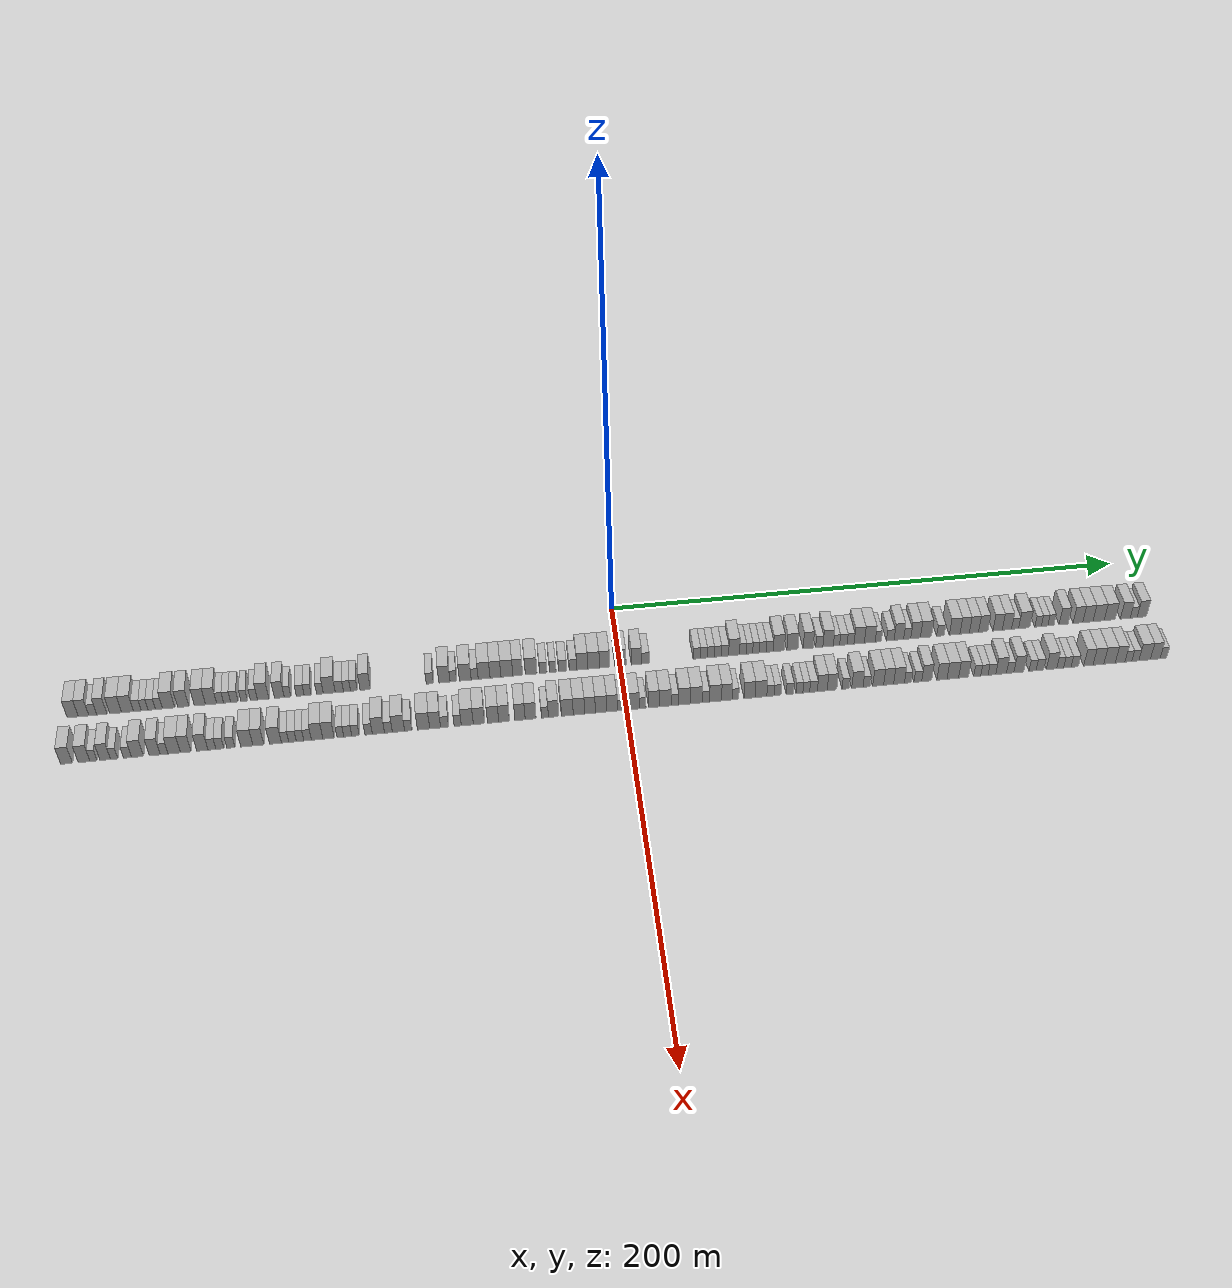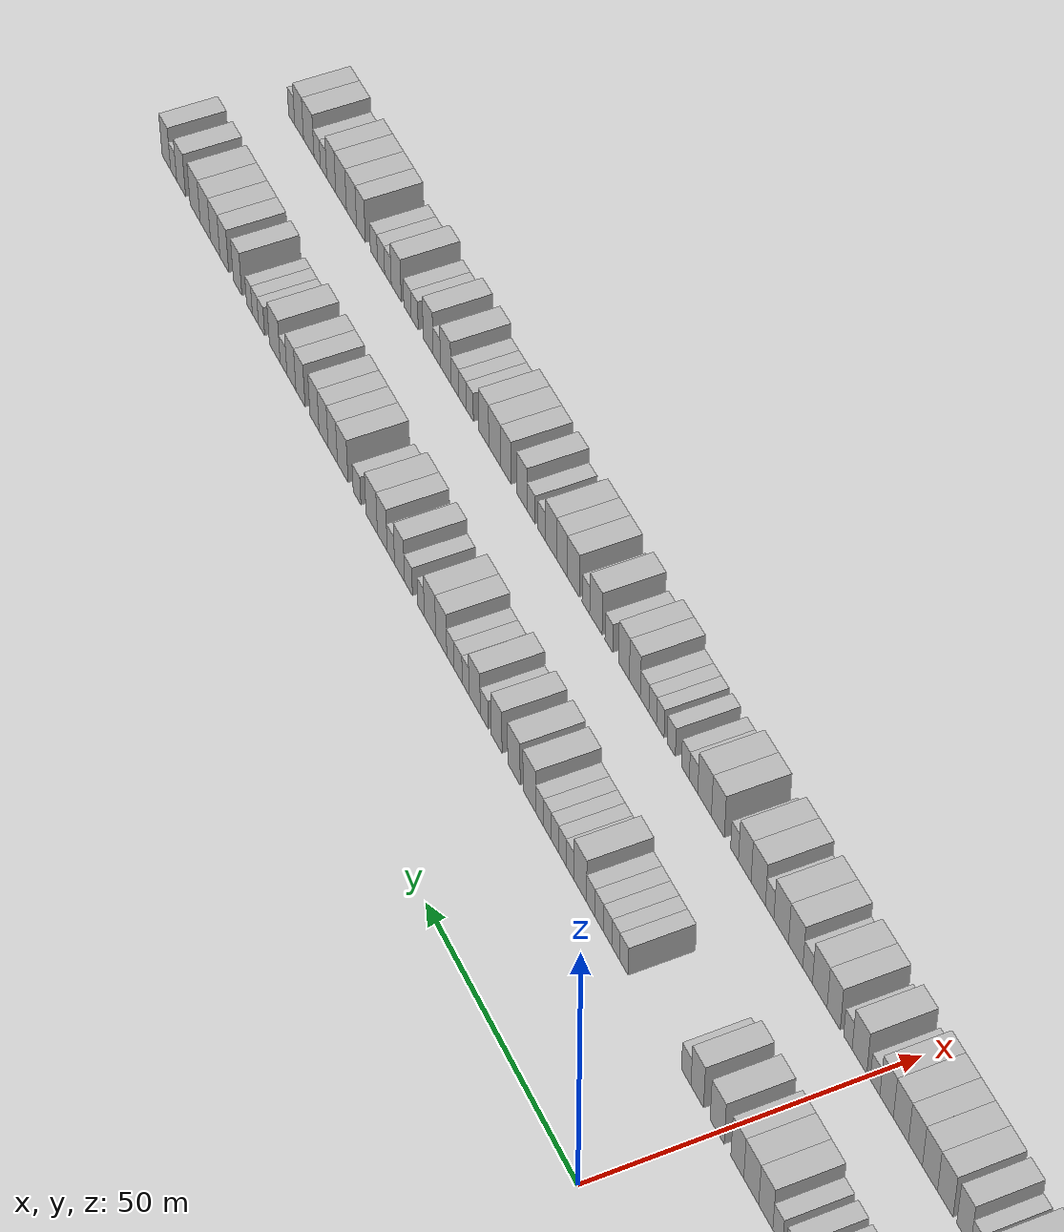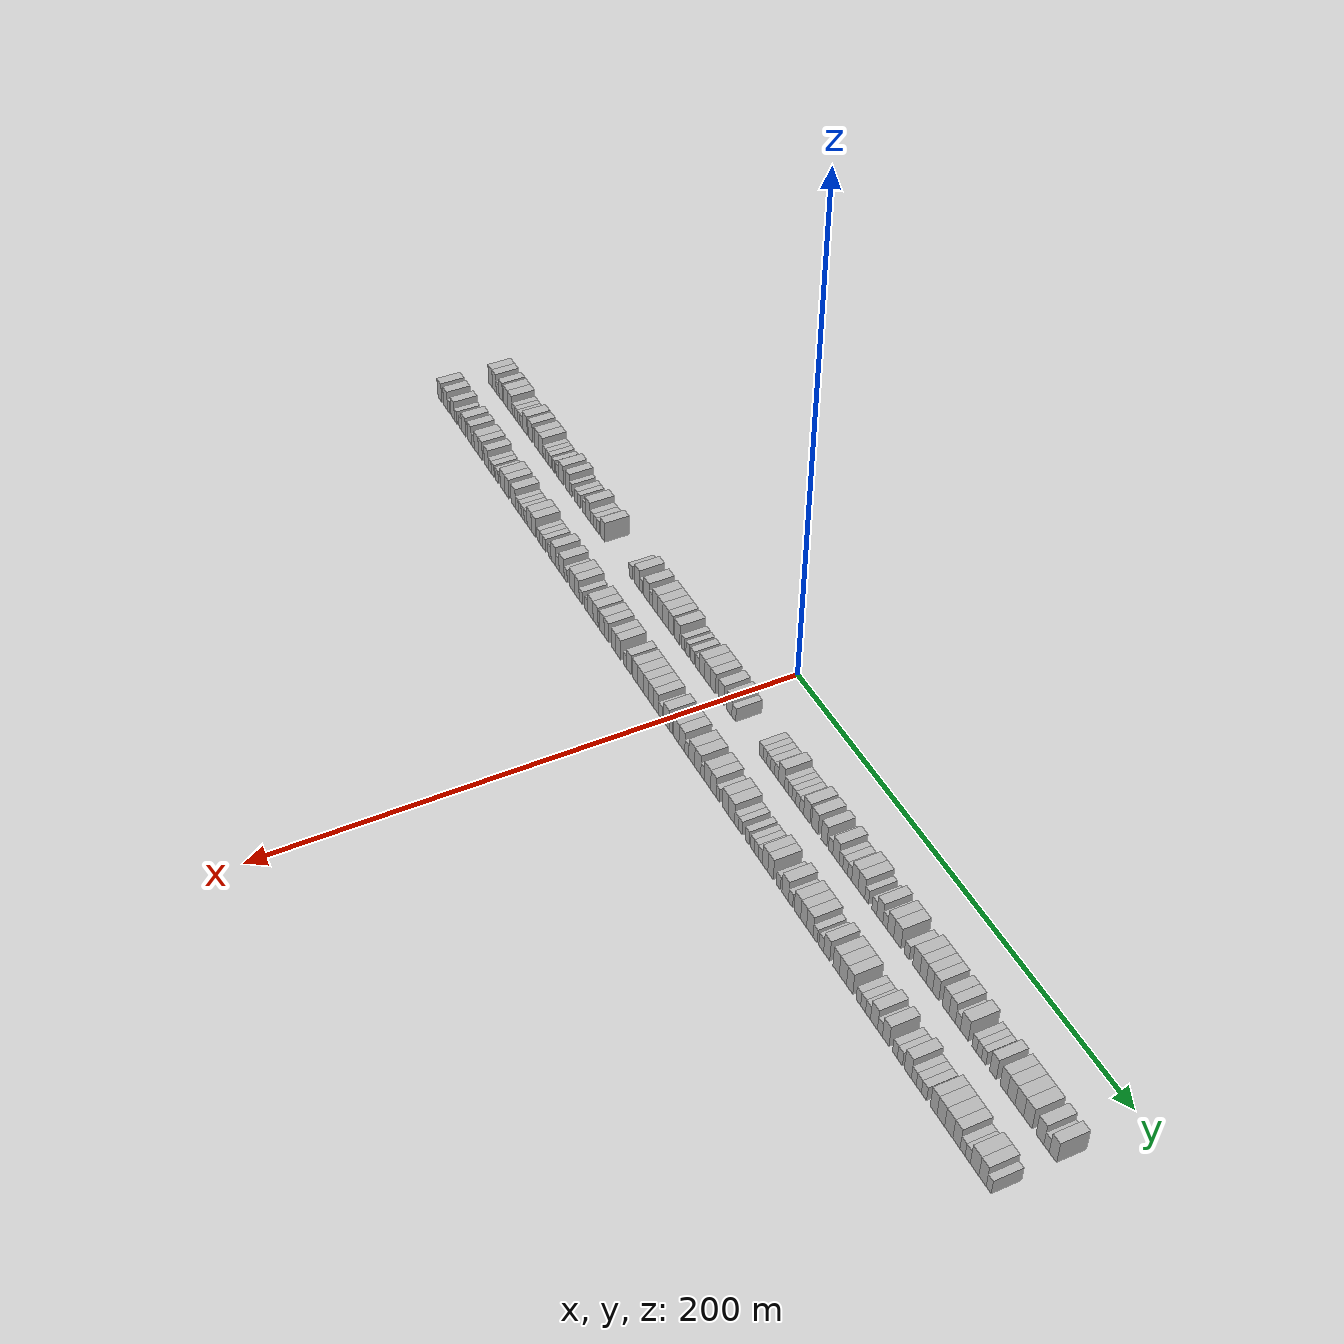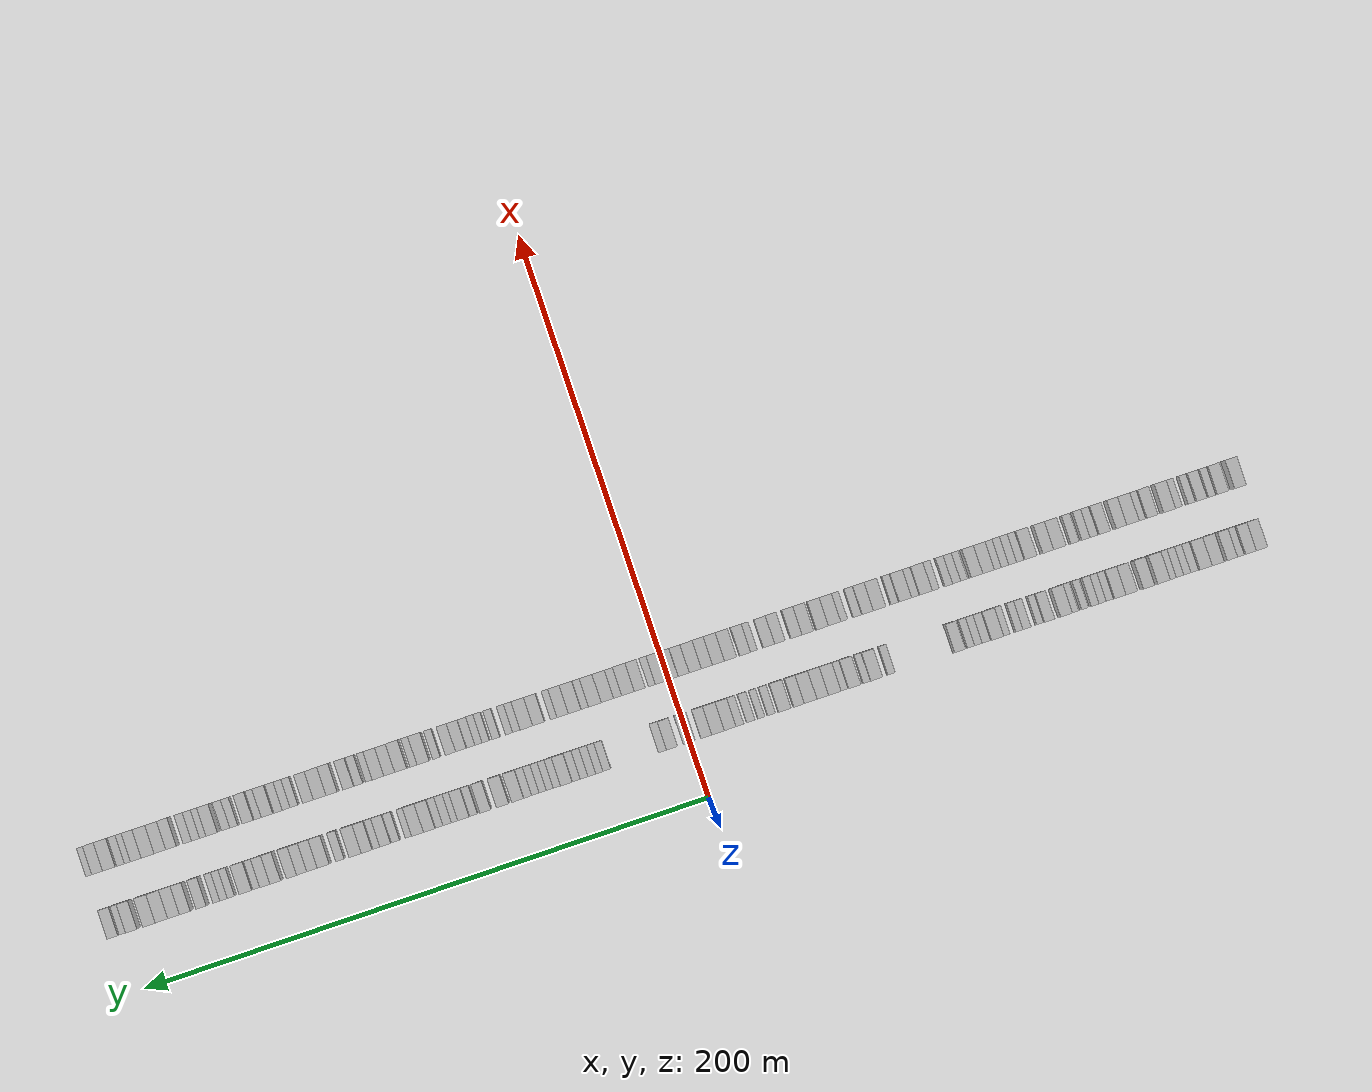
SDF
<sdf version="1.6">
 <world name="default">
  <scene>
   <sky><clouds><speed>12</speed></clouds></sky>
   <ambient>0.4 0.4 0.4 1</ambient>
   <background>0.7 0.7 0.7 1</background>
   <shadows>1</shadows>
  </scene>
  <gravity>0 0 -9.8066</gravity>
  <magnetic_field>6e-06 2.3e-05 -4.2e-05</magnetic_field>
  <physics default="0" name="default_physics" type="ode">
   <ode>
    <solver>
     <type>quick</type>
     <iters>10</iters>
     <sor>1.0</sor>
     <use_dynamic_moi_rescaling>0</use_dynamic_moi_rescaling>
    </solver>
    <constraints>
     <cfm>0</cfm>
     <erp>0.2</erp>
     <contact_max_correcting_vel>100</contact_max_correcting_vel>
     <contact_surface_layer>0.001</contact_surface_layer>
    </constraints>
   </ode>
   <max_step_size>0.004</max_step_size>
   <real_time_factor>1</real_time_factor>
   <real_time_update_rate>250</real_time_update_rate>
  </physics>
  <light name="sun" type="directional">
   <pose>0 0 10 0 0 0</pose>
   <diffuse>0.8 0.8 0.8 1</diffuse>
   <specular>0.2 0.2 0.2 1</specular>
   <attenuation>
    <range>1000</range>
    <constant>0.9</constant>
    <linear>0.01</linear>
    <quadratic>0.001</quadratic>
   </attenuation>
   <direction>-0.5 0.1 -0.9</direction>
  </light>
  <model name="building_1">
   <static>1</static>
   <pose>25.0000 -202.0031 0 0.000000 0.000000 0.000000</pose>
   <link name="link">
    <pose>0 0 4.50 0 0 0</pose>
    <collision name="collision"><geometry><box><size>10.0000 3.9939 9.0000</size></box></geometry></collision>
    <visual name="visual">
     <cast_shadows>0</cast_shadows>
     <geometry><box><size>10.0000 3.9939 9.0000</size></box></geometry>
     <material>
      <script>
       <uri>model://HANNAS_wall/materials/scripts</uri>
       <uri>model://HANNAS_wall/materials/textures</uri>
       <name>vrc/HANNAS_wall</name>
      </script>
     </material>
    </visual>
   </link>
  </model>
  <model name="building_2">
   <static>1</static>
   <pose>25.0000 -198.1215 0 0.000000 0.000000 0.000000</pose>
   <link name="link">
    <pose>0 0 4.50 0 0 0</pose>
    <collision name="collision"><geometry><box><size>10.0000 3.7692 9.0000</size></box></geometry></collision>
    <visual name="visual">
     <cast_shadows>0</cast_shadows>
     <geometry><box><size>10.0000 3.7692 9.0000</size></box></geometry>
     <material>
      <script>
       <uri>model://HANNAS_wall/materials/scripts</uri>
       <uri>model://HANNAS_wall/materials/textures</uri>
       <name>vrc/HANNAS_wall</name>
      </script>
     </material>
    </visual>
   </link>
  </model>
  <model name="building_3">
   <static>1</static>
   <pose>25.0000 -194.8044 0 0.000000 0.000000 0.000000</pose>
   <link name="link">
    <pose>0 0 3.00 0 0 0</pose>
    <collision name="collision"><geometry><box><size>10.0000 2.8649 6.0000</size></box></geometry></collision>
    <visual name="visual">
     <cast_shadows>0</cast_shadows>
     <geometry><box><size>10.0000 2.8649 6.0000</size></box></geometry>
     <material>
      <script>
       <uri>model://HANNAS_wall/materials/scripts</uri>
       <uri>model://HANNAS_wall/materials/textures</uri>
       <name>vrc/HANNAS_wall</name>
      </script>
     </material>
    </visual>
   </link>
  </model>
  <model name="building_4">
   <static>1</static>
   <pose>25.0000 -191.5345 0 0.000000 0.000000 0.000000</pose>
   <link name="link">
    <pose>0 0 4.50 0 0 0</pose>
    <collision name="collision"><geometry><box><size>10.0000 3.6749 9.0000</size></box></geometry></collision>
    <visual name="visual">
     <cast_shadows>0</cast_shadows>
     <geometry><box><size>10.0000 3.6749 9.0000</size></box></geometry>
     <material>
      <script>
       <uri>model://HANNAS_wall/materials/scripts</uri>
       <uri>model://HANNAS_wall/materials/textures</uri>
       <name>vrc/HANNAS_wall</name>
      </script>
     </material>
    </visual>
   </link>
  </model>
  <model name="building_5">
   <static>1</static>
   <pose>25.0000 -186.5516 0 0.000000 0.000000 0.000000</pose>
   <link name="link">
    <pose>0 0 4.50 0 0 0</pose>
    <collision name="collision"><geometry><box><size>10.0000 4.2910 9.0000</size></box></geometry></collision>
    <visual name="visual">
     <cast_shadows>0</cast_shadows>
     <geometry><box><size>10.0000 4.2910 9.0000</size></box></geometry>
     <material>
      <script>
       <uri>model://HANNAS_wall/materials/scripts</uri>
       <uri>model://HANNAS_wall/materials/textures</uri>
       <name>vrc/HANNAS_wall</name>
      </script>
     </material>
    </visual>
   </link>
  </model>
  <model name="building_6">
   <static>1</static>
   <pose>25.0000 -182.2381 0 0.000000 0.000000 0.000000</pose>
   <link name="link">
    <pose>0 0 4.50 0 0 0</pose>
    <collision name="collision"><geometry><box><size>10.0000 4.3360 9.0000</size></box></geometry></collision>
    <visual name="visual">
     <cast_shadows>0</cast_shadows>
     <geometry><box><size>10.0000 4.3360 9.0000</size></box></geometry>
     <material>
      <script>
       <uri>model://HANNAS_wall/materials/scripts</uri>
       <uri>model://HANNAS_wall/materials/textures</uri>
       <name>vrc/HANNAS_wall</name>
      </script>
     </material>
    </visual>
   </link>
  </model>
  <model name="building_7">
   <static>1</static>
   <pose>25.0000 -178.7124 0 0.000000 0.000000 0.000000</pose>
   <link name="link">
    <pose>0 0 3.00 0 0 0</pose>
    <collision name="collision"><geometry><box><size>10.0000 2.7153 6.0000</size></box></geometry></collision>
    <visual name="visual">
     <cast_shadows>0</cast_shadows>
     <geometry><box><size>10.0000 2.7153 6.0000</size></box></geometry>
     <material>
      <script>
       <uri>model://HANNAS_wall/materials/scripts</uri>
       <uri>model://HANNAS_wall/materials/textures</uri>
       <name>vrc/HANNAS_wall</name>
      </script>
     </material>
    </visual>
   </link>
  </model>
  <model name="building_8">
   <static>1</static>
   <pose>25.0000 -176.1058 0 0.000000 0.000000 0.000000</pose>
   <link name="link">
    <pose>0 0 3.00 0 0 0</pose>
    <collision name="collision"><geometry><box><size>10.0000 2.4980 6.0000</size></box></geometry></collision>
    <visual name="visual">
     <cast_shadows>0</cast_shadows>
     <geometry><box><size>10.0000 2.4980 6.0000</size></box></geometry>
     <material>
      <script>
       <uri>model://HANNAS_wall/materials/scripts</uri>
       <uri>model://HANNAS_wall/materials/textures</uri>
       <name>vrc/HANNAS_wall</name>
      </script>
     </material>
    </visual>
   </link>
  </model>
  <model name="building_9">
   <static>1</static>
   <pose>25.0000 -173.5377 0 0.000000 0.000000 0.000000</pose>
   <link name="link">
    <pose>0 0 3.00 0 0 0</pose>
    <collision name="collision"><geometry><box><size>10.0000 2.6382 6.0000</size></box></geometry></collision>
    <visual name="visual">
     <cast_shadows>0</cast_shadows>
     <geometry><box><size>10.0000 2.6382 6.0000</size></box></geometry>
     <material>
      <script>
       <uri>model://HANNAS_wall/materials/scripts</uri>
       <uri>model://HANNAS_wall/materials/textures</uri>
       <name>vrc/HANNAS_wall</name>
      </script>
     </material>
    </visual>
   </link>
  </model>
  <model name="building_10">
   <static>1</static>
   <pose>25.0000 -170.9153 0 0.000000 0.000000 0.000000</pose>
   <link name="link">
    <pose>0 0 3.00 0 0 0</pose>
    <collision name="collision"><geometry><box><size>10.0000 2.6066 6.0000</size></box></geometry></collision>
    <visual name="visual">
     <cast_shadows>0</cast_shadows>
     <geometry><box><size>10.0000 2.6066 6.0000</size></box></geometry>
     <material>
      <script>
       <uri>model://HANNAS_wall/materials/scripts</uri>
       <uri>model://HANNAS_wall/materials/textures</uri>
       <name>vrc/HANNAS_wall</name>
      </script>
     </material>
    </visual>
   </link>
  </model>
  <model name="building_11">
   <static>1</static>
   <pose>25.0000 -167.3863 0 0.000000 0.000000 0.000000</pose>
   <link name="link">
    <pose>0 0 4.50 0 0 0</pose>
    <collision name="collision"><geometry><box><size>10.0000 4.4516 9.0000</size></box></geometry></collision>
    <visual name="visual">
     <cast_shadows>0</cast_shadows>
     <geometry><box><size>10.0000 4.4516 9.0000</size></box></geometry>
     <material>
      <script>
       <uri>model://HANNAS_wall/materials/scripts</uri>
       <uri>model://HANNAS_wall/materials/textures</uri>
       <name>vrc/HANNAS_wall</name>
      </script>
     </material>
    </visual>
   </link>
  </model>
  <model name="building_12">
   <static>1</static>
   <pose>25.0000 -162.1167 0 0.000000 0.000000 0.000000</pose>
   <link name="link">
    <pose>0 0 4.50 0 0 0</pose>
    <collision name="collision"><geometry><box><size>10.0000 4.0875 9.0000</size></box></geometry></collision>
    <visual name="visual">
     <cast_shadows>0</cast_shadows>
     <geometry><box><size>10.0000 4.0875 9.0000</size></box></geometry>
     <material>
      <script>
       <uri>model://HANNAS_wall/materials/scripts</uri>
       <uri>model://HANNAS_wall/materials/textures</uri>
       <name>vrc/HANNAS_wall</name>
      </script>
     </material>
    </visual>
   </link>
  </model>
  <model name="building_13">
   <static>1</static>
   <pose>25.0000 -156.0221 0 0.000000 0.000000 0.000000</pose>
   <link name="link">
    <pose>0 0 4.50 0 0 0</pose>
    <collision name="collision"><geometry><box><size>10.0000 4.1019 9.0000</size></box></geometry></collision>
    <visual name="visual">
     <cast_shadows>0</cast_shadows>
     <geometry><box><size>10.0000 4.1019 9.0000</size></box></geometry>
     <material>
      <script>
       <uri>model://HANNAS_wall/materials/scripts</uri>
       <uri>model://HANNAS_wall/materials/textures</uri>
       <name>vrc/HANNAS_wall</name>
      </script>
     </material>
    </visual>
   </link>
  </model>
  <model name="building_14">
   <static>1</static>
   <pose>25.0000 -151.9481 0 0.000000 0.000000 0.000000</pose>
   <link name="link">
    <pose>0 0 4.50 0 0 0</pose>
    <collision name="collision"><geometry><box><size>10.0000 4.0460 9.0000</size></box></geometry></collision>
    <visual name="visual">
     <cast_shadows>0</cast_shadows>
     <geometry><box><size>10.0000 4.0460 9.0000</size></box></geometry>
     <material>
      <script>
       <uri>model://HANNAS_wall/materials/scripts</uri>
       <uri>model://HANNAS_wall/materials/textures</uri>
       <name>vrc/HANNAS_wall</name>
      </script>
     </material>
    </visual>
   </link>
  </model>
  <model name="building_15">
   <static>1</static>
   <pose>25.0000 -148.6582 0 0.000000 0.000000 0.000000</pose>
   <link name="link">
    <pose>0 0 3.00 0 0 0</pose>
    <collision name="collision"><geometry><box><size>10.0000 2.5339 6.0000</size></box></geometry></collision>
    <visual name="visual">
     <cast_shadows>0</cast_shadows>
     <geometry><box><size>10.0000 2.5339 6.0000</size></box></geometry>
     <material>
      <script>
       <uri>model://HANNAS_wall/materials/scripts</uri>
       <uri>model://HANNAS_wall/materials/textures</uri>
       <name>vrc/HANNAS_wall</name>
      </script>
     </material>
    </visual>
   </link>
  </model>
  <model name="building_16">
   <static>1</static>
   <pose>25.0000 -146.1278 0 0.000000 0.000000 0.000000</pose>
   <link name="link">
    <pose>0 0 3.00 0 0 0</pose>
    <collision name="collision"><geometry><box><size>10.0000 2.5267 6.0000</size></box></geometry></collision>
    <visual name="visual">
     <cast_shadows>0</cast_shadows>
     <geometry><box><size>10.0000 2.5267 6.0000</size></box></geometry>
     <material>
      <script>
       <uri>model://HANNAS_wall/materials/scripts</uri>
       <uri>model://HANNAS_wall/materials/textures</uri>
       <name>vrc/HANNAS_wall</name>
      </script>
     </material>
    </visual>
   </link>
  </model>
  <model name="building_17">
   <static>1</static>
   <pose>25.0000 -143.4757 0 0.000000 0.000000 0.000000</pose>
   <link name="link">
    <pose>0 0 3.00 0 0 0</pose>
    <collision name="collision"><geometry><box><size>10.0000 2.7776 6.0000</size></box></geometry></collision>
    <visual name="visual">
     <cast_shadows>0</cast_shadows>
     <geometry><box><size>10.0000 2.7776 6.0000</size></box></geometry>
     <material>
      <script>
       <uri>model://HANNAS_wall/materials/scripts</uri>
       <uri>model://HANNAS_wall/materials/textures</uri>
       <name>vrc/HANNAS_wall</name>
      </script>
     </material>
    </visual>
   </link>
  </model>
  <model name="building_18">
   <static>1</static>
   <pose>25.0000 -139.8715 0 0.000000 0.000000 0.000000</pose>
   <link name="link">
    <pose>0 0 3.00 0 0 0</pose>
    <collision name="collision"><geometry><box><size>10.0000 2.4307 6.0000</size></box></geometry></collision>
    <visual name="visual">
     <cast_shadows>0</cast_shadows>
     <geometry><box><size>10.0000 2.4307 6.0000</size></box></geometry>
     <material>
      <script>
       <uri>model://HANNAS_wall/materials/scripts</uri>
       <uri>model://HANNAS_wall/materials/textures</uri>
       <name>vrc/HANNAS_wall</name>
      </script>
     </material>
    </visual>
   </link>
  </model>
  <model name="building_19">
   <static>1</static>
   <pose>25.0000 -136.3448 0 0.000000 0.000000 0.000000</pose>
   <link name="link">
    <pose>0 0 3.00 0 0 0</pose>
    <collision name="collision"><geometry><box><size>10.0000 2.6228 6.0000</size></box></geometry></collision>
    <visual name="visual">
     <cast_shadows>0</cast_shadows>
     <geometry><box><size>10.0000 2.6228 6.0000</size></box></geometry>
     <material>
      <script>
       <uri>model://HANNAS_wall/materials/scripts</uri>
       <uri>model://HANNAS_wall/materials/textures</uri>
       <name>vrc/HANNAS_wall</name>
      </script>
     </material>
    </visual>
   </link>
  </model>
  <model name="building_20">
   <static>1</static>
   <pose>25.0000 -132.9356 0 0.000000 0.000000 0.000000</pose>
   <link name="link">
    <pose>0 0 4.50 0 0 0</pose>
    <collision name="collision"><geometry><box><size>10.0000 4.1955 9.0000</size></box></geometry></collision>
    <visual name="visual">
     <cast_shadows>0</cast_shadows>
     <geometry><box><size>10.0000 4.1955 9.0000</size></box></geometry>
     <material>
      <script>
       <uri>model://HANNAS_wall/materials/scripts</uri>
       <uri>model://HANNAS_wall/materials/textures</uri>
       <name>vrc/HANNAS_wall</name>
      </script>
     </material>
    </visual>
   </link>
  </model>
  <model name="building_21">
   <static>1</static>
   <pose>25.0000 -127.0183 0 0.000000 0.000000 0.000000</pose>
   <link name="link">
    <pose>0 0 4.50 0 0 0</pose>
    <collision name="collision"><geometry><box><size>10.0000 3.6392 9.0000</size></box></geometry></collision>
    <visual name="visual">
     <cast_shadows>0</cast_shadows>
     <geometry><box><size>10.0000 3.6392 9.0000</size></box></geometry>
     <material>
      <script>
       <uri>model://HANNAS_wall/materials/scripts</uri>
       <uri>model://HANNAS_wall/materials/textures</uri>
       <name>vrc/HANNAS_wall</name>
      </script>
     </material>
    </visual>
   </link>
  </model>
  <model name="building_22">
   <static>1</static>
   <pose>25.0000 -123.9982 0 0.000000 0.000000 0.000000</pose>
   <link name="link">
    <pose>0 0 3.00 0 0 0</pose>
    <collision name="collision"><geometry><box><size>10.0000 2.4009 6.0000</size></box></geometry></collision>
    <visual name="visual">
     <cast_shadows>0</cast_shadows>
     <geometry><box><size>10.0000 2.4009 6.0000</size></box></geometry>
     <material>
      <script>
       <uri>model://HANNAS_wall/materials/scripts</uri>
       <uri>model://HANNAS_wall/materials/textures</uri>
       <name>vrc/HANNAS_wall</name>
      </script>
     </material>
    </visual>
   </link>
  </model>
  <model name="building_23">
   <static>1</static>
   <pose>25.0000 -119.3594 0 0.000000 0.000000 0.000000</pose>
   <link name="link">
    <pose>0 0 3.00 0 0 0</pose>
    <collision name="collision"><geometry><box><size>10.0000 2.8768 6.0000</size></box></geometry></collision>
    <visual name="visual">
     <cast_shadows>0</cast_shadows>
     <geometry><box><size>10.0000 2.8768 6.0000</size></box></geometry>
     <material>
      <script>
       <uri>model://HANNAS_wall/materials/scripts</uri>
       <uri>model://HANNAS_wall/materials/textures</uri>
       <name>vrc/HANNAS_wall</name>
      </script>
     </material>
    </visual>
   </link>
  </model>
  <model name="building_24">
   <static>1</static>
   <pose>25.0000 -116.6311 0 0.000000 0.000000 0.000000</pose>
   <link name="link">
    <pose>0 0 3.00 0 0 0</pose>
    <collision name="collision"><geometry><box><size>10.0000 2.5799 6.0000</size></box></geometry></collision>
    <visual name="visual">
     <cast_shadows>0</cast_shadows>
     <geometry><box><size>10.0000 2.5799 6.0000</size></box></geometry>
     <material>
      <script>
       <uri>model://HANNAS_wall/materials/scripts</uri>
       <uri>model://HANNAS_wall/materials/textures</uri>
       <name>vrc/HANNAS_wall</name>
      </script>
     </material>
    </visual>
   </link>
  </model>
  <model name="building_25">
   <static>1</static>
   <pose>25.0000 -112.0945 0 0.000000 0.000000 0.000000</pose>
   <link name="link">
    <pose>0 0 3.00 0 0 0</pose>
    <collision name="collision"><geometry><box><size>10.0000 2.4932 6.0000</size></box></geometry></collision>
    <visual name="visual">
     <cast_shadows>0</cast_shadows>
     <geometry><box><size>10.0000 2.4932 6.0000</size></box></geometry>
     <material>
      <script>
       <uri>model://HANNAS_wall/materials/scripts</uri>
       <uri>model://HANNAS_wall/materials/textures</uri>
       <name>vrc/HANNAS_wall</name>
      </script>
     </material>
    </visual>
   </link>
  </model>
  <model name="building_26">
   <static>1</static>
   <pose>25.0000 -108.6519 0 0.000000 0.000000 0.000000</pose>
   <link name="link">
    <pose>0 0 4.50 0 0 0</pose>
    <collision name="collision"><geometry><box><size>10.0000 4.3920 9.0000</size></box></geometry></collision>
    <visual name="visual">
     <cast_shadows>0</cast_shadows>
     <geometry><box><size>10.0000 4.3920 9.0000</size></box></geometry>
     <material>
      <script>
       <uri>model://HANNAS_wall/materials/scripts</uri>
       <uri>model://HANNAS_wall/materials/textures</uri>
       <name>vrc/HANNAS_wall</name>
      </script>
     </material>
    </visual>
   </link>
  </model>
  <model name="building_27">
   <static>1</static>
   <pose>25.0000 -104.9623 0 0.000000 0.000000 0.000000</pose>
   <link name="link">
    <pose>0 0 3.00 0 0 0</pose>
    <collision name="collision"><geometry><box><size>10.0000 2.9872 6.0000</size></box></geometry></collision>
    <visual name="visual">
     <cast_shadows>0</cast_shadows>
     <geometry><box><size>10.0000 2.9872 6.0000</size></box></geometry>
     <material>
      <script>
       <uri>model://HANNAS_wall/materials/scripts</uri>
       <uri>model://HANNAS_wall/materials/textures</uri>
       <name>vrc/HANNAS_wall</name>
      </script>
     </material>
    </visual>
   </link>
  </model>
  <model name="building_28">
   <static>1</static>
   <pose>25.0000 -102.1458 0 0.000000 0.000000 0.000000</pose>
   <link name="link">
    <pose>0 0 3.00 0 0 0</pose>
    <collision name="collision"><geometry><box><size>10.0000 2.6458 6.0000</size></box></geometry></collision>
    <visual name="visual">
     <cast_shadows>0</cast_shadows>
     <geometry><box><size>10.0000 2.6458 6.0000</size></box></geometry>
     <material>
      <script>
       <uri>model://HANNAS_wall/materials/scripts</uri>
       <uri>model://HANNAS_wall/materials/textures</uri>
       <name>vrc/HANNAS_wall</name>
      </script>
     </material>
    </visual>
   </link>
  </model>
  <model name="building_29">
   <static>1</static>
   <pose>25.0000 -99.5724 0 0.000000 0.000000 0.000000</pose>
   <link name="link">
    <pose>0 0 3.00 0 0 0</pose>
    <collision name="collision"><geometry><box><size>10.0000 2.5010 6.0000</size></box></geometry></collision>
    <visual name="visual">
     <cast_shadows>0</cast_shadows>
     <geometry><box><size>10.0000 2.5010 6.0000</size></box></geometry>
     <material>
      <script>
       <uri>model://HANNAS_wall/materials/scripts</uri>
       <uri>model://HANNAS_wall/materials/textures</uri>
       <name>vrc/HANNAS_wall</name>
      </script>
     </material>
    </visual>
   </link>
  </model>
  <model name="building_30">
   <static>1</static>
   <pose>25.0000 -95.3956 0 0.000000 0.000000 0.000000</pose>
   <link name="link">
    <pose>0 0 4.50 0 0 0</pose>
    <collision name="collision"><geometry><box><size>10.0000 3.8526 9.0000</size></box></geometry></collision>
    <visual name="visual">
     <cast_shadows>0</cast_shadows>
     <geometry><box><size>10.0000 3.8526 9.0000</size></box></geometry>
     <material>
      <script>
       <uri>model://HANNAS_wall/materials/scripts</uri>
       <uri>model://HANNAS_wall/materials/textures</uri>
       <name>vrc/HANNAS_wall</name>
      </script>
     </material>
    </visual>
   </link>
  </model>
  <model name="building_31">
   <static>1</static>
   <pose>25.0000 -71.4348 0 0.000000 0.000000 0.000000</pose>
   <link name="link">
    <pose>0 0 3.00 0 0 0</pose>
    <collision name="collision"><geometry><box><size>10.0000 2.6896 6.0000</size></box></geometry></collision>
    <visual name="visual">
     <cast_shadows>0</cast_shadows>
     <geometry><box><size>10.0000 2.6896 6.0000</size></box></geometry>
     <material>
      <script>
       <uri>model://HANNAS_wall/materials/scripts</uri>
       <uri>model://HANNAS_wall/materials/textures</uri>
       <name>vrc/HANNAS_wall</name>
      </script>
     </material>
    </visual>
   </link>
  </model>
  <model name="building_32">
   <static>1</static>
   <pose>25.0000 -66.0001 0 0.000000 0.000000 0.000000</pose>
   <link name="link">
    <pose>0 0 4.50 0 0 0</pose>
    <collision name="collision"><geometry><box><size>10.0000 4.1798 9.0000</size></box></geometry></collision>
    <visual name="visual">
     <cast_shadows>0</cast_shadows>
     <geometry><box><size>10.0000 4.1798 9.0000</size></box></geometry>
     <material>
      <script>
       <uri>model://HANNAS_wall/materials/scripts</uri>
       <uri>model://HANNAS_wall/materials/textures</uri>
       <name>vrc/HANNAS_wall</name>
      </script>
     </material>
    </visual>
   </link>
  </model>
  <model name="building_33">
   <static>1</static>
   <pose>25.0000 -62.6714 0 0.000000 0.000000 0.000000</pose>
   <link name="link">
    <pose>0 0 3.00 0 0 0</pose>
    <collision name="collision"><geometry><box><size>10.0000 2.4775 6.0000</size></box></geometry></collision>
    <visual name="visual">
     <cast_shadows>0</cast_shadows>
     <geometry><box><size>10.0000 2.4775 6.0000</size></box></geometry>
     <material>
      <script>
       <uri>model://HANNAS_wall/materials/scripts</uri>
       <uri>model://HANNAS_wall/materials/textures</uri>
       <name>vrc/HANNAS_wall</name>
      </script>
     </material>
    </visual>
   </link>
  </model>
  <model name="building_34">
   <static>1</static>
   <pose>25.0000 -58.2343 0 0.000000 0.000000 0.000000</pose>
   <link name="link">
    <pose>0 0 4.50 0 0 0</pose>
    <collision name="collision"><geometry><box><size>10.0000 4.3966 9.0000</size></box></geometry></collision>
    <visual name="visual">
     <cast_shadows>0</cast_shadows>
     <geometry><box><size>10.0000 4.3966 9.0000</size></box></geometry>
     <material>
      <script>
       <uri>model://HANNAS_wall/materials/scripts</uri>
       <uri>model://HANNAS_wall/materials/textures</uri>
       <name>vrc/HANNAS_wall</name>
      </script>
     </material>
    </visual>
   </link>
  </model>
  <model name="building_35">
   <static>1</static>
   <pose>25.0000 -54.7356 0 0.000000 0.000000 0.000000</pose>
   <link name="link">
    <pose>0 0 3.00 0 0 0</pose>
    <collision name="collision"><geometry><box><size>10.0000 2.6008 6.0000</size></box></geometry></collision>
    <visual name="visual">
     <cast_shadows>0</cast_shadows>
     <geometry><box><size>10.0000 2.6008 6.0000</size></box></geometry>
     <material>
      <script>
       <uri>model://HANNAS_wall/materials/scripts</uri>
       <uri>model://HANNAS_wall/materials/textures</uri>
       <name>vrc/HANNAS_wall</name>
      </script>
     </material>
    </visual>
   </link>
  </model>
  <model name="building_36">
   <static>1</static>
   <pose>25.0000 -51.2147 0 0.000000 0.000000 0.000000</pose>
   <link name="link">
    <pose>0 0 4.50 0 0 0</pose>
    <collision name="collision"><geometry><box><size>10.0000 4.4411 9.0000</size></box></geometry></collision>
    <visual name="visual">
     <cast_shadows>0</cast_shadows>
     <geometry><box><size>10.0000 4.4411 9.0000</size></box></geometry>
     <material>
      <script>
       <uri>model://HANNAS_wall/materials/scripts</uri>
       <uri>model://HANNAS_wall/materials/textures</uri>
       <name>vrc/HANNAS_wall</name>
      </script>
     </material>
    </visual>
   </link>
  </model>
  <model name="building_37">
   <static>1</static>
   <pose>25.0000 -46.9516 0 0.000000 0.000000 0.000000</pose>
   <link name="link">
    <pose>0 0 4.50 0 0 0</pose>
    <collision name="collision"><geometry><box><size>10.0000 4.0851 9.0000</size></box></geometry></collision>
    <visual name="visual">
     <cast_shadows>0</cast_shadows>
     <geometry><box><size>10.0000 4.0851 9.0000</size></box></geometry>
     <material>
      <script>
       <uri>model://HANNAS_wall/materials/scripts</uri>
       <uri>model://HANNAS_wall/materials/textures</uri>
       <name>vrc/HANNAS_wall</name>
      </script>
     </material>
    </visual>
   </link>
  </model>
  <model name="building_38">
   <static>1</static>
   <pose>25.0000 -42.6696 0 0.000000 0.000000 0.000000</pose>
   <link name="link">
    <pose>0 0 4.50 0 0 0</pose>
    <collision name="collision"><geometry><box><size>10.0000 4.4789 9.0000</size></box></geometry></collision>
    <visual name="visual">
     <cast_shadows>0</cast_shadows>
     <geometry><box><size>10.0000 4.4789 9.0000</size></box></geometry>
     <material>
      <script>
       <uri>model://HANNAS_wall/materials/scripts</uri>
       <uri>model://HANNAS_wall/materials/textures</uri>
       <name>vrc/HANNAS_wall</name>
      </script>
     </material>
    </visual>
   </link>
  </model>
  <model name="building_39">
   <static>1</static>
   <pose>25.0000 -38.5943 0 0.000000 0.000000 0.000000</pose>
   <link name="link">
    <pose>0 0 4.50 0 0 0</pose>
    <collision name="collision"><geometry><box><size>10.0000 3.6718 9.0000</size></box></geometry></collision>
    <visual name="visual">
     <cast_shadows>0</cast_shadows>
     <geometry><box><size>10.0000 3.6718 9.0000</size></box></geometry>
     <material>
      <script>
       <uri>model://HANNAS_wall/materials/scripts</uri>
       <uri>model://HANNAS_wall/materials/textures</uri>
       <name>vrc/HANNAS_wall</name>
      </script>
     </material>
    </visual>
   </link>
  </model>
  <model name="building_40">
   <static>1</static>
   <pose>25.0000 -33.5643 0 0.000000 0.000000 0.000000</pose>
   <link name="link">
    <pose>0 0 4.50 0 0 0</pose>
    <collision name="collision"><geometry><box><size>10.0000 4.3882 9.0000</size></box></geometry></collision>
    <visual name="visual">
     <cast_shadows>0</cast_shadows>
     <geometry><box><size>10.0000 4.3882 9.0000</size></box></geometry>
     <material>
      <script>
       <uri>model://HANNAS_wall/materials/scripts</uri>
       <uri>model://HANNAS_wall/materials/textures</uri>
       <name>vrc/HANNAS_wall</name>
      </script>
     </material>
    </visual>
   </link>
  </model>
  <model name="building_41">
   <static>1</static>
   <pose>25.0000 -28.9870 0 0.000000 0.000000 0.000000</pose>
   <link name="link">
    <pose>0 0 3.00 0 0 0</pose>
    <collision name="collision"><geometry><box><size>10.0000 2.7664 6.0000</size></box></geometry></collision>
    <visual name="visual">
     <cast_shadows>0</cast_shadows>
     <geometry><box><size>10.0000 2.7664 6.0000</size></box></geometry>
     <material>
      <script>
       <uri>model://HANNAS_wall/materials/scripts</uri>
       <uri>model://HANNAS_wall/materials/textures</uri>
       <name>vrc/HANNAS_wall</name>
      </script>
     </material>
    </visual>
   </link>
  </model>
  <model name="building_42">
   <static>1</static>
   <pose>25.0000 -25.3923 0 0.000000 0.000000 0.000000</pose>
   <link name="link">
    <pose>0 0 3.00 0 0 0</pose>
    <collision name="collision"><geometry><box><size>10.0000 2.4228 6.0000</size></box></geometry></collision>
    <visual name="visual">
     <cast_shadows>0</cast_shadows>
     <geometry><box><size>10.0000 2.4228 6.0000</size></box></geometry>
     <material>
      <script>
       <uri>model://HANNAS_wall/materials/scripts</uri>
       <uri>model://HANNAS_wall/materials/textures</uri>
       <name>vrc/HANNAS_wall</name>
      </script>
     </material>
    </visual>
   </link>
  </model>
  <model name="building_43">
   <static>1</static>
   <pose>25.0000 -21.6845 0 0.000000 0.000000 0.000000</pose>
   <link name="link">
    <pose>0 0 3.00 0 0 0</pose>
    <collision name="collision"><geometry><box><size>10.0000 2.9929 6.0000</size></box></geometry></collision>
    <visual name="visual">
     <cast_shadows>0</cast_shadows>
     <geometry><box><size>10.0000 2.9929 6.0000</size></box></geometry>
     <material>
      <script>
       <uri>model://HANNAS_wall/materials/scripts</uri>
       <uri>model://HANNAS_wall/materials/textures</uri>
       <name>vrc/HANNAS_wall</name>
      </script>
     </material>
    </visual>
   </link>
  </model>
  <model name="building_44">
   <static>1</static>
   <pose>25.0000 -17.7682 0 0.000000 0.000000 0.000000</pose>
   <link name="link">
    <pose>0 0 3.00 0 0 0</pose>
    <collision name="collision"><geometry><box><size>10.0000 2.8396 6.0000</size></box></geometry></collision>
    <visual name="visual">
     <cast_shadows>0</cast_shadows>
     <geometry><box><size>10.0000 2.8396 6.0000</size></box></geometry>
     <material>
      <script>
       <uri>model://HANNAS_wall/materials/scripts</uri>
       <uri>model://HANNAS_wall/materials/textures</uri>
       <name>vrc/HANNAS_wall</name>
      </script>
     </material>
    </visual>
   </link>
  </model>
  <model name="building_45">
   <static>1</static>
   <pose>25.0000 -14.2849 0 0.000000 0.000000 0.000000</pose>
   <link name="link">
    <pose>0 0 4.50 0 0 0</pose>
    <collision name="collision"><geometry><box><size>10.0000 4.1270 9.0000</size></box></geometry></collision>
    <visual name="visual">
     <cast_shadows>0</cast_shadows>
     <geometry><box><size>10.0000 4.1270 9.0000</size></box></geometry>
     <material>
      <script>
       <uri>model://HANNAS_wall/materials/scripts</uri>
       <uri>model://HANNAS_wall/materials/textures</uri>
       <name>vrc/HANNAS_wall</name>
      </script>
     </material>
    </visual>
   </link>
  </model>
  <model name="building_46">
   <static>1</static>
   <pose>25.0000 -10.0117 0 0.000000 0.000000 0.000000</pose>
   <link name="link">
    <pose>0 0 4.50 0 0 0</pose>
    <collision name="collision"><geometry><box><size>10.0000 4.4192 9.0000</size></box></geometry></collision>
    <visual name="visual">
     <cast_shadows>0</cast_shadows>
     <geometry><box><size>10.0000 4.4192 9.0000</size></box></geometry>
     <material>
      <script>
       <uri>model://HANNAS_wall/materials/scripts</uri>
       <uri>model://HANNAS_wall/materials/textures</uri>
       <name>vrc/HANNAS_wall</name>
      </script>
     </material>
    </visual>
   </link>
  </model>
  <model name="building_47">
   <static>1</static>
   <pose>25.0000 -5.8763 0 0.000000 0.000000 0.000000</pose>
   <link name="link">
    <pose>0 0 4.50 0 0 0</pose>
    <collision name="collision"><geometry><box><size>10.0000 3.8517 9.0000</size></box></geometry></collision>
    <visual name="visual">
     <cast_shadows>0</cast_shadows>
     <geometry><box><size>10.0000 3.8517 9.0000</size></box></geometry>
     <material>
      <script>
       <uri>model://HANNAS_wall/materials/scripts</uri>
       <uri>model://HANNAS_wall/materials/textures</uri>
       <name>vrc/HANNAS_wall</name>
      </script>
     </material>
    </visual>
   </link>
  </model>
  <model name="building_48">
   <static>1</static>
   <pose>25.0000 0.1629 0 0.000000 0.000000 0.000000</pose>
   <link name="link">
    <pose>0 0 4.50 0 0 0</pose>
    <collision name="collision"><geometry><box><size>10.0000 4.2267 9.0000</size></box></geometry></collision>
    <visual name="visual">
     <cast_shadows>0</cast_shadows>
     <geometry><box><size>10.0000 4.2267 9.0000</size></box></geometry>
     <material>
      <script>
       <uri>model://HANNAS_wall/materials/scripts</uri>
       <uri>model://HANNAS_wall/materials/textures</uri>
       <name>vrc/HANNAS_wall</name>
      </script>
     </material>
    </visual>
   </link>
  </model>
  <model name="building_49">
   <static>1</static>
   <pose>25.0000 6.2037 0 0.000000 0.000000 0.000000</pose>
   <link name="link">
    <pose>0 0 4.50 0 0 0</pose>
    <collision name="collision"><geometry><box><size>10.0000 3.8548 9.0000</size></box></geometry></collision>
    <visual name="visual">
     <cast_shadows>0</cast_shadows>
     <geometry><box><size>10.0000 3.8548 9.0000</size></box></geometry>
     <material>
      <script>
       <uri>model://HANNAS_wall/materials/scripts</uri>
       <uri>model://HANNAS_wall/materials/textures</uri>
       <name>vrc/HANNAS_wall</name>
      </script>
     </material>
    </visual>
   </link>
  </model>
  <model name="building_50">
   <static>1</static>
   <pose>25.0000 9.5866 0 0.000000 0.000000 0.000000</pose>
   <link name="link">
    <pose>0 0 3.00 0 0 0</pose>
    <collision name="collision"><geometry><box><size>10.0000 2.9111 6.0000</size></box></geometry></collision>
    <visual name="visual">
     <cast_shadows>0</cast_shadows>
     <geometry><box><size>10.0000 2.9111 6.0000</size></box></geometry>
     <material>
      <script>
       <uri>model://HANNAS_wall/materials/scripts</uri>
       <uri>model://HANNAS_wall/materials/textures</uri>
       <name>vrc/HANNAS_wall</name>
      </script>
     </material>
    </visual>
   </link>
  </model>
  <model name="building_51">
   <static>1</static>
   <pose>25.0000 29.2199 0 0.000000 0.000000 0.000000</pose>
   <link name="link">
    <pose>0 0 3.00 0 0 0</pose>
    <collision name="collision"><geometry><box><size>10.0000 2.7852 6.0000</size></box></geometry></collision>
    <visual name="visual">
     <cast_shadows>0</cast_shadows>
     <geometry><box><size>10.0000 2.7852 6.0000</size></box></geometry>
     <material>
      <script>
       <uri>model://HANNAS_wall/materials/scripts</uri>
       <uri>model://HANNAS_wall/materials/textures</uri>
       <name>vrc/HANNAS_wall</name>
      </script>
     </material>
    </visual>
   </link>
  </model>
  <model name="building_52">
   <static>1</static>
   <pose>25.0000 31.8865 0 0.000000 0.000000 0.000000</pose>
   <link name="link">
    <pose>0 0 3.00 0 0 0</pose>
    <collision name="collision"><geometry><box><size>10.0000 2.5481 6.0000</size></box></geometry></collision>
    <visual name="visual">
     <cast_shadows>0</cast_shadows>
     <geometry><box><size>10.0000 2.5481 6.0000</size></box></geometry>
     <material>
      <script>
       <uri>model://HANNAS_wall/materials/scripts</uri>
       <uri>model://HANNAS_wall/materials/textures</uri>
       <name>vrc/HANNAS_wall</name>
      </script>
     </material>
    </visual>
   </link>
  </model>
  <model name="building_53">
   <static>1</static>
   <pose>25.0000 34.5204 0 0.000000 0.000000 0.000000</pose>
   <link name="link">
    <pose>0 0 3.00 0 0 0</pose>
    <collision name="collision"><geometry><box><size>10.0000 2.7196 6.0000</size></box></geometry></collision>
    <visual name="visual">
     <cast_shadows>0</cast_shadows>
     <geometry><box><size>10.0000 2.7196 6.0000</size></box></geometry>
     <material>
      <script>
       <uri>model://HANNAS_wall/materials/scripts</uri>
       <uri>model://HANNAS_wall/materials/textures</uri>
       <name>vrc/HANNAS_wall</name>
      </script>
     </material>
    </visual>
   </link>
  </model>
  <model name="building_54">
   <static>1</static>
   <pose>25.0000 37.2696 0 0.000000 0.000000 0.000000</pose>
   <link name="link">
    <pose>0 0 3.00 0 0 0</pose>
    <collision name="collision"><geometry><box><size>10.0000 2.7787 6.0000</size></box></geometry></collision>
    <visual name="visual">
     <cast_shadows>0</cast_shadows>
     <geometry><box><size>10.0000 2.7787 6.0000</size></box></geometry>
     <material>
      <script>
       <uri>model://HANNAS_wall/materials/scripts</uri>
       <uri>model://HANNAS_wall/materials/textures</uri>
       <name>vrc/HANNAS_wall</name>
      </script>
     </material>
    </visual>
   </link>
  </model>
  <model name="building_55">
   <static>1</static>
   <pose>25.0000 40.0288 0 0.000000 0.000000 0.000000</pose>
   <link name="link">
    <pose>0 0 3.00 0 0 0</pose>
    <collision name="collision"><geometry><box><size>10.0000 2.7397 6.0000</size></box></geometry></collision>
    <visual name="visual">
     <cast_shadows>0</cast_shadows>
     <geometry><box><size>10.0000 2.7397 6.0000</size></box></geometry>
     <material>
      <script>
       <uri>model://HANNAS_wall/materials/scripts</uri>
       <uri>model://HANNAS_wall/materials/textures</uri>
       <name>vrc/HANNAS_wall</name>
      </script>
     </material>
    </visual>
   </link>
  </model>
  <model name="building_56">
   <static>1</static>
   <pose>25.0000 43.4785 0 0.000000 0.000000 0.000000</pose>
   <link name="link">
    <pose>0 0 4.50 0 0 0</pose>
    <collision name="collision"><geometry><box><size>10.0000 4.1596 9.0000</size></box></geometry></collision>
    <visual name="visual">
     <cast_shadows>0</cast_shadows>
     <geometry><box><size>10.0000 4.1596 9.0000</size></box></geometry>
     <material>
      <script>
       <uri>model://HANNAS_wall/materials/scripts</uri>
       <uri>model://HANNAS_wall/materials/textures</uri>
       <name>vrc/HANNAS_wall</name>
      </script>
     </material>
    </visual>
   </link>
  </model>
  <model name="building_57">
   <static>1</static>
   <pose>25.0000 46.8566 0 0.000000 0.000000 0.000000</pose>
   <link name="link">
    <pose>0 0 3.00 0 0 0</pose>
    <collision name="collision"><geometry><box><size>10.0000 2.5967 6.0000</size></box></geometry></collision>
    <visual name="visual">
     <cast_shadows>0</cast_shadows>
     <geometry><box><size>10.0000 2.5967 6.0000</size></box></geometry>
     <material>
      <script>
       <uri>model://HANNAS_wall/materials/scripts</uri>
       <uri>model://HANNAS_wall/materials/textures</uri>
       <name>vrc/HANNAS_wall</name>
      </script>
     </material>
    </visual>
   </link>
  </model>
  <model name="building_58">
   <static>1</static>
   <pose>25.0000 49.3823 0 0.000000 0.000000 0.000000</pose>
   <link name="link">
    <pose>0 0 3.00 0 0 0</pose>
    <collision name="collision"><geometry><box><size>10.0000 2.4547 6.0000</size></box></geometry></collision>
    <visual name="visual">
     <cast_shadows>0</cast_shadows>
     <geometry><box><size>10.0000 2.4547 6.0000</size></box></geometry>
     <material>
      <script>
       <uri>model://HANNAS_wall/materials/scripts</uri>
       <uri>model://HANNAS_wall/materials/textures</uri>
       <name>vrc/HANNAS_wall</name>
      </script>
     </material>
    </visual>
   </link>
  </model>
  <model name="building_59">
   <static>1</static>
   <pose>25.0000 51.8646 0 0.000000 0.000000 0.000000</pose>
   <link name="link">
    <pose>0 0 3.00 0 0 0</pose>
    <collision name="collision"><geometry><box><size>10.0000 2.5100 6.0000</size></box></geometry></collision>
    <visual name="visual">
     <cast_shadows>0</cast_shadows>
     <geometry><box><size>10.0000 2.5100 6.0000</size></box></geometry>
     <material>
      <script>
       <uri>model://HANNAS_wall/materials/scripts</uri>
       <uri>model://HANNAS_wall/materials/textures</uri>
       <name>vrc/HANNAS_wall</name>
      </script>
     </material>
    </visual>
   </link>
  </model>
  <model name="building_60">
   <static>1</static>
   <pose>25.0000 54.4542 0 0.000000 0.000000 0.000000</pose>
   <link name="link">
    <pose>0 0 3.00 0 0 0</pose>
    <collision name="collision"><geometry><box><size>10.0000 2.6693 6.0000</size></box></geometry></collision>
    <visual name="visual">
     <cast_shadows>0</cast_shadows>
     <geometry><box><size>10.0000 2.6693 6.0000</size></box></geometry>
     <material>
      <script>
       <uri>model://HANNAS_wall/materials/scripts</uri>
       <uri>model://HANNAS_wall/materials/textures</uri>
       <name>vrc/HANNAS_wall</name>
      </script>
     </material>
    </visual>
   </link>
  </model>
  <model name="building_61">
   <static>1</static>
   <pose>25.0000 57.1441 0 0.000000 0.000000 0.000000</pose>
   <link name="link">
    <pose>0 0 3.00 0 0 0</pose>
    <collision name="collision"><geometry><box><size>10.0000 2.7105 6.0000</size></box></geometry></collision>
    <visual name="visual">
     <cast_shadows>0</cast_shadows>
     <geometry><box><size>10.0000 2.7105 6.0000</size></box></geometry>
     <material>
      <script>
       <uri>model://HANNAS_wall/materials/scripts</uri>
       <uri>model://HANNAS_wall/materials/textures</uri>
       <name>vrc/HANNAS_wall</name>
      </script>
     </material>
    </visual>
   </link>
  </model>
  <model name="building_62">
   <static>1</static>
   <pose>25.0000 60.6363 0 0.000000 0.000000 0.000000</pose>
   <link name="link">
    <pose>0 0 4.50 0 0 0</pose>
    <collision name="collision"><geometry><box><size>10.0000 4.2738 9.0000</size></box></geometry></collision>
    <visual name="visual">
     <cast_shadows>0</cast_shadows>
     <geometry><box><size>10.0000 4.2738 9.0000</size></box></geometry>
     <material>
      <script>
       <uri>model://HANNAS_wall/materials/scripts</uri>
       <uri>model://HANNAS_wall/materials/textures</uri>
       <name>vrc/HANNAS_wall</name>
      </script>
     </material>
    </visual>
   </link>
  </model>
  <model name="building_63">
   <static>1</static>
   <pose>25.0000 65.9166 0 0.000000 0.000000 0.000000</pose>
   <link name="link">
    <pose>0 0 4.50 0 0 0</pose>
    <collision name="collision"><geometry><box><size>10.0000 4.2868 9.0000</size></box></geometry></collision>
    <visual name="visual">
     <cast_shadows>0</cast_shadows>
     <geometry><box><size>10.0000 4.2868 9.0000</size></box></geometry>
     <material>
      <script>
       <uri>model://HANNAS_wall/materials/scripts</uri>
       <uri>model://HANNAS_wall/materials/textures</uri>
       <name>vrc/HANNAS_wall</name>
      </script>
     </material>
    </visual>
   </link>
  </model>
  <model name="building_64">
   <static>1</static>
   <pose>25.0000 71.9795 0 0.000000 0.000000 0.000000</pose>
   <link name="link">
    <pose>0 0 4.50 0 0 0</pose>
    <collision name="collision"><geometry><box><size>10.0000 3.8390 9.0000</size></box></geometry></collision>
    <visual name="visual">
     <cast_shadows>0</cast_shadows>
     <geometry><box><size>10.0000 3.8390 9.0000</size></box></geometry>
     <material>
      <script>
       <uri>model://HANNAS_wall/materials/scripts</uri>
       <uri>model://HANNAS_wall/materials/textures</uri>
       <name>vrc/HANNAS_wall</name>
      </script>
     </material>
    </visual>
   </link>
  </model>
  <model name="building_65">
   <static>1</static>
   <pose>25.0000 76.3048 0 0.000000 0.000000 0.000000</pose>
   <link name="link">
    <pose>0 0 3.00 0 0 0</pose>
    <collision name="collision"><geometry><box><size>10.0000 2.8117 6.0000</size></box></geometry></collision>
    <visual name="visual">
     <cast_shadows>0</cast_shadows>
     <geometry><box><size>10.0000 2.8117 6.0000</size></box></geometry>
     <material>
      <script>
       <uri>model://HANNAS_wall/materials/scripts</uri>
       <uri>model://HANNAS_wall/materials/textures</uri>
       <name>vrc/HANNAS_wall</name>
      </script>
     </material>
    </visual>
   </link>
  </model>
  <model name="building_66">
   <static>1</static>
   <pose>25.0000 79.7198 0 0.000000 0.000000 0.000000</pose>
   <link name="link">
    <pose>0 0 4.50 0 0 0</pose>
    <collision name="collision"><geometry><box><size>10.0000 4.0183 9.0000</size></box></geometry></collision>
    <visual name="visual">
     <cast_shadows>0</cast_shadows>
     <geometry><box><size>10.0000 4.0183 9.0000</size></box></geometry>
     <material>
      <script>
       <uri>model://HANNAS_wall/materials/scripts</uri>
       <uri>model://HANNAS_wall/materials/textures</uri>
       <name>vrc/HANNAS_wall</name>
      </script>
     </material>
    </visual>
   </link>
  </model>
  <model name="building_67">
   <static>1</static>
   <pose>25.0000 82.9447 0 0.000000 0.000000 0.000000</pose>
   <link name="link">
    <pose>0 0 3.00 0 0 0</pose>
    <collision name="collision"><geometry><box><size>10.0000 2.4314 6.0000</size></box></geometry></collision>
    <visual name="visual">
     <cast_shadows>0</cast_shadows>
     <geometry><box><size>10.0000 2.4314 6.0000</size></box></geometry>
     <material>
      <script>
       <uri>model://HANNAS_wall/materials/scripts</uri>
       <uri>model://HANNAS_wall/materials/textures</uri>
       <name>vrc/HANNAS_wall</name>
      </script>
     </material>
    </visual>
   </link>
  </model>
  <model name="building_68">
   <static>1</static>
   <pose>25.0000 85.6265 0 0.000000 0.000000 0.000000</pose>
   <link name="link">
    <pose>0 0 3.00 0 0 0</pose>
    <collision name="collision"><geometry><box><size>10.0000 2.9322 6.0000</size></box></geometry></collision>
    <visual name="visual">
     <cast_shadows>0</cast_shadows>
     <geometry><box><size>10.0000 2.9322 6.0000</size></box></geometry>
     <material>
      <script>
       <uri>model://HANNAS_wall/materials/scripts</uri>
       <uri>model://HANNAS_wall/materials/textures</uri>
       <name>vrc/HANNAS_wall</name>
      </script>
     </material>
    </visual>
   </link>
  </model>
  <model name="building_69">
   <static>1</static>
   <pose>25.0000 88.4260 0 0.000000 0.000000 0.000000</pose>
   <link name="link">
    <pose>0 0 3.00 0 0 0</pose>
    <collision name="collision"><geometry><box><size>10.0000 2.6669 6.0000</size></box></geometry></collision>
    <visual name="visual">
     <cast_shadows>0</cast_shadows>
     <geometry><box><size>10.0000 2.6669 6.0000</size></box></geometry>
     <material>
      <script>
       <uri>model://HANNAS_wall/materials/scripts</uri>
       <uri>model://HANNAS_wall/materials/textures</uri>
       <name>vrc/HANNAS_wall</name>
      </script>
     </material>
    </visual>
   </link>
  </model>
  <model name="building_70">
   <static>1</static>
   <pose>25.0000 91.7732 0 0.000000 0.000000 0.000000</pose>
   <link name="link">
    <pose>0 0 4.50 0 0 0</pose>
    <collision name="collision"><geometry><box><size>10.0000 4.0275 9.0000</size></box></geometry></collision>
    <visual name="visual">
     <cast_shadows>0</cast_shadows>
     <geometry><box><size>10.0000 4.0275 9.0000</size></box></geometry>
     <material>
      <script>
       <uri>model://HANNAS_wall/materials/scripts</uri>
       <uri>model://HANNAS_wall/materials/textures</uri>
       <name>vrc/HANNAS_wall</name>
      </script>
     </material>
    </visual>
   </link>
  </model>
  <model name="building_71">
   <static>1</static>
   <pose>25.0000 95.8864 0 0.000000 0.000000 0.000000</pose>
   <link name="link">
    <pose>0 0 4.50 0 0 0</pose>
    <collision name="collision"><geometry><box><size>10.0000 4.1989 9.0000</size></box></geometry></collision>
    <visual name="visual">
     <cast_shadows>0</cast_shadows>
     <geometry><box><size>10.0000 4.1989 9.0000</size></box></geometry>
     <material>
      <script>
       <uri>model://HANNAS_wall/materials/scripts</uri>
       <uri>model://HANNAS_wall/materials/textures</uri>
       <name>vrc/HANNAS_wall</name>
      </script>
     </material>
    </visual>
   </link>
  </model>
  <model name="building_72">
   <static>1</static>
   <pose>25.0000 99.1921 0 0.000000 0.000000 0.000000</pose>
   <link name="link">
    <pose>0 0 3.00 0 0 0</pose>
    <collision name="collision"><geometry><box><size>10.0000 2.4126 6.0000</size></box></geometry></collision>
    <visual name="visual">
     <cast_shadows>0</cast_shadows>
     <geometry><box><size>10.0000 2.4126 6.0000</size></box></geometry>
     <material>
      <script>
       <uri>model://HANNAS_wall/materials/scripts</uri>
       <uri>model://HANNAS_wall/materials/textures</uri>
       <name>vrc/HANNAS_wall</name>
      </script>
     </material>
    </visual>
   </link>
  </model>
  <model name="building_73">
   <static>1</static>
   <pose>25.0000 103.8671 0 0.000000 0.000000 0.000000</pose>
   <link name="link">
    <pose>0 0 3.00 0 0 0</pose>
    <collision name="collision"><geometry><box><size>10.0000 2.9373 6.0000</size></box></geometry></collision>
    <visual name="visual">
     <cast_shadows>0</cast_shadows>
     <geometry><box><size>10.0000 2.9373 6.0000</size></box></geometry>
     <material>
      <script>
       <uri>model://HANNAS_wall/materials/scripts</uri>
       <uri>model://HANNAS_wall/materials/textures</uri>
       <name>vrc/HANNAS_wall</name>
      </script>
     </material>
    </visual>
   </link>
  </model>
  <model name="building_74">
   <static>1</static>
   <pose>25.0000 107.2173 0 0.000000 0.000000 0.000000</pose>
   <link name="link">
    <pose>0 0 4.50 0 0 0</pose>
    <collision name="collision"><geometry><box><size>10.0000 3.7632 9.0000</size></box></geometry></collision>
    <visual name="visual">
     <cast_shadows>0</cast_shadows>
     <geometry><box><size>10.0000 3.7632 9.0000</size></box></geometry>
     <material>
      <script>
       <uri>model://HANNAS_wall/materials/scripts</uri>
       <uri>model://HANNAS_wall/materials/textures</uri>
       <name>vrc/HANNAS_wall</name>
      </script>
     </material>
    </visual>
   </link>
  </model>
  <model name="building_75">
   <static>1</static>
   <pose>25.0000 110.4770 0 0.000000 0.000000 0.000000</pose>
   <link name="link">
    <pose>0 0 3.00 0 0 0</pose>
    <collision name="collision"><geometry><box><size>10.0000 2.7562 6.0000</size></box></geometry></collision>
    <visual name="visual">
     <cast_shadows>0</cast_shadows>
     <geometry><box><size>10.0000 2.7562 6.0000</size></box></geometry>
     <material>
      <script>
       <uri>model://HANNAS_wall/materials/scripts</uri>
       <uri>model://HANNAS_wall/materials/textures</uri>
       <name>vrc/HANNAS_wall</name>
      </script>
     </material>
    </visual>
   </link>
  </model>
  <model name="building_76">
   <static>1</static>
   <pose>25.0000 113.7417 0 0.000000 0.000000 0.000000</pose>
   <link name="link">
    <pose>0 0 4.50 0 0 0</pose>
    <collision name="collision"><geometry><box><size>10.0000 3.7732 9.0000</size></box></geometry></collision>
    <visual name="visual">
     <cast_shadows>0</cast_shadows>
     <geometry><box><size>10.0000 3.7732 9.0000</size></box></geometry>
     <material>
      <script>
       <uri>model://HANNAS_wall/materials/scripts</uri>
       <uri>model://HANNAS_wall/materials/textures</uri>
       <name>vrc/HANNAS_wall</name>
      </script>
     </material>
    </visual>
   </link>
  </model>
  <model name="building_77">
   <static>1</static>
   <pose>25.0000 117.8129 0 0.000000 0.000000 0.000000</pose>
   <link name="link">
    <pose>0 0 4.50 0 0 0</pose>
    <collision name="collision"><geometry><box><size>10.0000 4.3692 9.0000</size></box></geometry></collision>
    <visual name="visual">
     <cast_shadows>0</cast_shadows>
     <geometry><box><size>10.0000 4.3692 9.0000</size></box></geometry>
     <material>
      <script>
       <uri>model://HANNAS_wall/materials/scripts</uri>
       <uri>model://HANNAS_wall/materials/textures</uri>
       <name>vrc/HANNAS_wall</name>
      </script>
     </material>
    </visual>
   </link>
  </model>
  <model name="building_78">
   <static>1</static>
   <pose>25.0000 123.4860 0 0.000000 0.000000 0.000000</pose>
   <link name="link">
    <pose>0 0 3.00 0 0 0</pose>
    <collision name="collision"><geometry><box><size>10.0000 2.9769 6.0000</size></box></geometry></collision>
    <visual name="visual">
     <cast_shadows>0</cast_shadows>
     <geometry><box><size>10.0000 2.9769 6.0000</size></box></geometry>
     <material>
      <script>
       <uri>model://HANNAS_wall/materials/scripts</uri>
       <uri>model://HANNAS_wall/materials/textures</uri>
       <name>vrc/HANNAS_wall</name>
      </script>
     </material>
    </visual>
   </link>
  </model>
  <model name="building_79">
   <static>1</static>
   <pose>25.0000 129.0513 0 0.000000 0.000000 0.000000</pose>
   <link name="link">
    <pose>0 0 4.50 0 0 0</pose>
    <collision name="collision"><geometry><box><size>10.0000 4.1537 9.0000</size></box></geometry></collision>
    <visual name="visual">
     <cast_shadows>0</cast_shadows>
     <geometry><box><size>10.0000 4.1537 9.0000</size></box></geometry>
     <material>
      <script>
       <uri>model://HANNAS_wall/materials/scripts</uri>
       <uri>model://HANNAS_wall/materials/textures</uri>
       <name>vrc/HANNAS_wall</name>
      </script>
     </material>
    </visual>
   </link>
  </model>
  <model name="building_80">
   <static>1</static>
   <pose>25.0000 132.9724 0 0.000000 0.000000 0.000000</pose>
   <link name="link">
    <pose>0 0 4.50 0 0 0</pose>
    <collision name="collision"><geometry><box><size>10.0000 3.6885 9.0000</size></box></geometry></collision>
    <visual name="visual">
     <cast_shadows>0</cast_shadows>
     <geometry><box><size>10.0000 3.6885 9.0000</size></box></geometry>
     <material>
      <script>
       <uri>model://HANNAS_wall/materials/scripts</uri>
       <uri>model://HANNAS_wall/materials/textures</uri>
       <name>vrc/HANNAS_wall</name>
      </script>
     </material>
    </visual>
   </link>
  </model>
  <model name="building_81">
   <static>1</static>
   <pose>25.0000 136.6347 0 0.000000 0.000000 0.000000</pose>
   <link name="link">
    <pose>0 0 4.50 0 0 0</pose>
    <collision name="collision"><geometry><box><size>10.0000 3.6360 9.0000</size></box></geometry></collision>
    <visual name="visual">
     <cast_shadows>0</cast_shadows>
     <geometry><box><size>10.0000 3.6360 9.0000</size></box></geometry>
     <material>
      <script>
       <uri>model://HANNAS_wall/materials/scripts</uri>
       <uri>model://HANNAS_wall/materials/textures</uri>
       <name>vrc/HANNAS_wall</name>
      </script>
     </material>
    </visual>
   </link>
  </model>
  <model name="building_82">
   <static>1</static>
   <pose>25.0000 140.2624 0 0.000000 0.000000 0.000000</pose>
   <link name="link">
    <pose>0 0 4.50 0 0 0</pose>
    <collision name="collision"><geometry><box><size>10.0000 3.6195 9.0000</size></box></geometry></collision>
    <visual name="visual">
     <cast_shadows>0</cast_shadows>
     <geometry><box><size>10.0000 3.6195 9.0000</size></box></geometry>
     <material>
      <script>
       <uri>model://HANNAS_wall/materials/scripts</uri>
       <uri>model://HANNAS_wall/materials/textures</uri>
       <name>vrc/HANNAS_wall</name>
      </script>
     </material>
    </visual>
   </link>
  </model>
  <model name="building_83">
   <static>1</static>
   <pose>25.0000 145.9324 0 0.000000 0.000000 0.000000</pose>
   <link name="link">
    <pose>0 0 4.50 0 0 0</pose>
    <collision name="collision"><geometry><box><size>10.0000 3.7206 9.0000</size></box></geometry></collision>
    <visual name="visual">
     <cast_shadows>0</cast_shadows>
     <geometry><box><size>10.0000 3.7206 9.0000</size></box></geometry>
     <material>
      <script>
       <uri>model://HANNAS_wall/materials/scripts</uri>
       <uri>model://HANNAS_wall/materials/textures</uri>
       <name>vrc/HANNAS_wall</name>
      </script>
     </material>
    </visual>
   </link>
  </model>
  <model name="building_84">
   <static>1</static>
   <pose>25.0000 149.6136 0 0.000000 0.000000 0.000000</pose>
   <link name="link">
    <pose>0 0 4.50 0 0 0</pose>
    <collision name="collision"><geometry><box><size>10.0000 3.6417 9.0000</size></box></geometry></collision>
    <visual name="visual">
     <cast_shadows>0</cast_shadows>
     <geometry><box><size>10.0000 3.6417 9.0000</size></box></geometry>
     <material>
      <script>
       <uri>model://HANNAS_wall/materials/scripts</uri>
       <uri>model://HANNAS_wall/materials/textures</uri>
       <name>vrc/HANNAS_wall</name>
      </script>
     </material>
    </visual>
   </link>
  </model>
  <model name="building_85">
   <static>1</static>
   <pose>25.0000 152.8341 0 0.000000 0.000000 0.000000</pose>
   <link name="link">
    <pose>0 0 3.00 0 0 0</pose>
    <collision name="collision"><geometry><box><size>10.0000 2.7994 6.0000</size></box></geometry></collision>
    <visual name="visual">
     <cast_shadows>0</cast_shadows>
     <geometry><box><size>10.0000 2.7994 6.0000</size></box></geometry>
     <material>
      <script>
       <uri>model://HANNAS_wall/materials/scripts</uri>
       <uri>model://HANNAS_wall/materials/textures</uri>
       <name>vrc/HANNAS_wall</name>
      </script>
     </material>
    </visual>
   </link>
  </model>
  <model name="building_86">
   <static>1</static>
   <pose>25.0000 156.4471 0 0.000000 0.000000 0.000000</pose>
   <link name="link">
    <pose>0 0 4.50 0 0 0</pose>
    <collision name="collision"><geometry><box><size>10.0000 4.4266 9.0000</size></box></geometry></collision>
    <visual name="visual">
     <cast_shadows>0</cast_shadows>
     <geometry><box><size>10.0000 4.4266 9.0000</size></box></geometry>
     <material>
      <script>
       <uri>model://HANNAS_wall/materials/scripts</uri>
       <uri>model://HANNAS_wall/materials/textures</uri>
       <name>vrc/HANNAS_wall</name>
      </script>
     </material>
    </visual>
   </link>
  </model>
  <model name="building_87">
   <static>1</static>
   <pose>25.0000 161.9369 0 0.000000 0.000000 0.000000</pose>
   <link name="link">
    <pose>0 0 3.00 0 0 0</pose>
    <collision name="collision"><geometry><box><size>10.0000 2.5530 6.0000</size></box></geometry></collision>
    <visual name="visual">
     <cast_shadows>0</cast_shadows>
     <geometry><box><size>10.0000 2.5530 6.0000</size></box></geometry>
     <material>
      <script>
       <uri>model://HANNAS_wall/materials/scripts</uri>
       <uri>model://HANNAS_wall/materials/textures</uri>
       <name>vrc/HANNAS_wall</name>
      </script>
     </material>
    </visual>
   </link>
  </model>
  <model name="building_88">
   <static>1</static>
   <pose>25.0000 164.5136 0 0.000000 0.000000 0.000000</pose>
   <link name="link">
    <pose>0 0 3.00 0 0 0</pose>
    <collision name="collision"><geometry><box><size>10.0000 2.6004 6.0000</size></box></geometry></collision>
    <visual name="visual">
     <cast_shadows>0</cast_shadows>
     <geometry><box><size>10.0000 2.6004 6.0000</size></box></geometry>
     <material>
      <script>
       <uri>model://HANNAS_wall/materials/scripts</uri>
       <uri>model://HANNAS_wall/materials/textures</uri>
       <name>vrc/HANNAS_wall</name>
      </script>
     </material>
    </visual>
   </link>
  </model>
  <model name="building_89">
   <static>1</static>
   <pose>25.0000 167.0286 0 0.000000 0.000000 0.000000</pose>
   <link name="link">
    <pose>0 0 3.00 0 0 0</pose>
    <collision name="collision"><geometry><box><size>10.0000 2.4295 6.0000</size></box></geometry></collision>
    <visual name="visual">
     <cast_shadows>0</cast_shadows>
     <geometry><box><size>10.0000 2.4295 6.0000</size></box></geometry>
     <material>
      <script>
       <uri>model://HANNAS_wall/materials/scripts</uri>
       <uri>model://HANNAS_wall/materials/textures</uri>
       <name>vrc/HANNAS_wall</name>
      </script>
     </material>
    </visual>
   </link>
  </model>
  <model name="building_90">
   <static>1</static>
   <pose>25.0000 172.0446 0 0.000000 0.000000 0.000000</pose>
   <link name="link">
    <pose>0 0 4.50 0 0 0</pose>
    <collision name="collision"><geometry><box><size>10.0000 3.6026 9.0000</size></box></geometry></collision>
    <visual name="visual">
     <cast_shadows>0</cast_shadows>
     <geometry><box><size>10.0000 3.6026 9.0000</size></box></geometry>
     <material>
      <script>
       <uri>model://HANNAS_wall/materials/scripts</uri>
       <uri>model://HANNAS_wall/materials/textures</uri>
       <name>vrc/HANNAS_wall</name>
      </script>
     </material>
    </visual>
   </link>
  </model>
  <model name="building_91">
   <static>1</static>
   <pose>25.0000 177.7338 0 0.000000 0.000000 0.000000</pose>
   <link name="link">
    <pose>0 0 4.50 0 0 0</pose>
    <collision name="collision"><geometry><box><size>10.0000 3.7758 9.0000</size></box></geometry></collision>
    <visual name="visual">
     <cast_shadows>0</cast_shadows>
     <geometry><box><size>10.0000 3.7758 9.0000</size></box></geometry>
     <material>
      <script>
       <uri>model://HANNAS_wall/materials/scripts</uri>
       <uri>model://HANNAS_wall/materials/textures</uri>
       <name>vrc/HANNAS_wall</name>
      </script>
     </material>
    </visual>
   </link>
  </model>
  <model name="building_92">
   <static>1</static>
   <pose>25.0000 181.6630 0 0.000000 0.000000 0.000000</pose>
   <link name="link">
    <pose>0 0 4.50 0 0 0</pose>
    <collision name="collision"><geometry><box><size>10.0000 4.0826 9.0000</size></box></geometry></collision>
    <visual name="visual">
     <cast_shadows>0</cast_shadows>
     <geometry><box><size>10.0000 4.0826 9.0000</size></box></geometry>
     <material>
      <script>
       <uri>model://HANNAS_wall/materials/scripts</uri>
       <uri>model://HANNAS_wall/materials/textures</uri>
       <name>vrc/HANNAS_wall</name>
      </script>
     </material>
    </visual>
   </link>
  </model>
  <model name="building_93">
   <static>1</static>
   <pose>25.0000 185.9407 0 0.000000 0.000000 0.000000</pose>
   <link name="link">
    <pose>0 0 4.50 0 0 0</pose>
    <collision name="collision"><geometry><box><size>10.0000 4.4726 9.0000</size></box></geometry></collision>
    <visual name="visual">
     <cast_shadows>0</cast_shadows>
     <geometry><box><size>10.0000 4.4726 9.0000</size></box></geometry>
     <material>
      <script>
       <uri>model://HANNAS_wall/materials/scripts</uri>
       <uri>model://HANNAS_wall/materials/textures</uri>
       <name>vrc/HANNAS_wall</name>
      </script>
     </material>
    </visual>
   </link>
  </model>
  <model name="building_94">
   <static>1</static>
   <pose>25.0000 190.4036 0 0.000000 0.000000 0.000000</pose>
   <link name="link">
    <pose>0 0 4.50 0 0 0</pose>
    <collision name="collision"><geometry><box><size>10.0000 4.4531 9.0000</size></box></geometry></collision>
    <visual name="visual">
     <cast_shadows>0</cast_shadows>
     <geometry><box><size>10.0000 4.4531 9.0000</size></box></geometry>
     <material>
      <script>
       <uri>model://HANNAS_wall/materials/scripts</uri>
       <uri>model://HANNAS_wall/materials/textures</uri>
       <name>vrc/HANNAS_wall</name>
      </script>
     </material>
    </visual>
   </link>
  </model>
  <model name="building_95">
   <static>1</static>
   <pose>25.0000 196.6165 0 0.000000 0.000000 0.000000</pose>
   <link name="link">
    <pose>0 0 4.50 0 0 0</pose>
    <collision name="collision"><geometry><box><size>10.0000 3.9728 9.0000</size></box></geometry></collision>
    <visual name="visual">
     <cast_shadows>0</cast_shadows>
     <geometry><box><size>10.0000 3.9728 9.0000</size></box></geometry>
     <material>
      <script>
       <uri>model://HANNAS_wall/materials/scripts</uri>
       <uri>model://HANNAS_wall/materials/textures</uri>
       <name>vrc/HANNAS_wall</name>
      </script>
     </material>
    </visual>
   </link>
  </model>
  <model name="building_96">
   <static>1</static>
   <pose>25.0000 199.9591 0 0.000000 0.000000 0.000000</pose>
   <link name="link">
    <pose>0 0 3.00 0 0 0</pose>
    <collision name="collision"><geometry><box><size>10.0000 2.7123 6.0000</size></box></geometry></collision>
    <visual name="visual">
     <cast_shadows>0</cast_shadows>
     <geometry><box><size>10.0000 2.7123 6.0000</size></box></geometry>
     <material>
      <script>
       <uri>model://HANNAS_wall/materials/scripts</uri>
       <uri>model://HANNAS_wall/materials/textures</uri>
       <name>vrc/HANNAS_wall</name>
      </script>
     </material>
    </visual>
   </link>
  </model>
  <model name="building_97">
   <static>1</static>
   <pose>25.0000 203.2015 0 0.000000 0.000000 0.000000</pose>
   <link name="link">
    <pose>0 0 4.50 0 0 0</pose>
    <collision name="collision"><geometry><box><size>10.0000 3.7725 9.0000</size></box></geometry></collision>
    <visual name="visual">
     <cast_shadows>0</cast_shadows>
     <geometry><box><size>10.0000 3.7725 9.0000</size></box></geometry>
     <material>
      <script>
       <uri>model://HANNAS_wall/materials/scripts</uri>
       <uri>model://HANNAS_wall/materials/textures</uri>
       <name>vrc/HANNAS_wall</name>
      </script>
     </material>
    </visual>
   </link>
  </model>
  <model name="building_98">
   <static>1</static>
   <pose>47.0000 -201.9204 0 0.000000 0.000000 0.000000</pose>
   <link name="link">
    <pose>0 0 4.50 0 0 0</pose>
    <collision name="collision"><geometry><box><size>10.0000 4.1591 9.0000</size></box></geometry></collision>
    <visual name="visual">
     <cast_shadows>0</cast_shadows>
     <geometry><box><size>10.0000 4.1591 9.0000</size></box></geometry>
     <material>
      <script>
       <uri>model://HANNAS_wall/materials/scripts</uri>
       <uri>model://HANNAS_wall/materials/textures</uri>
       <name>vrc/HANNAS_wall</name>
      </script>
     </material>
    </visual>
   </link>
  </model>
  <model name="building_99">
   <static>1</static>
   <pose>47.0000 -195.7746 0 0.000000 0.000000 0.000000</pose>
   <link name="link">
    <pose>0 0 4.50 0 0 0</pose>
    <collision name="collision"><geometry><box><size>10.0000 4.1327 9.0000</size></box></geometry></collision>
    <visual name="visual">
     <cast_shadows>0</cast_shadows>
     <geometry><box><size>10.0000 4.1327 9.0000</size></box></geometry>
     <material>
      <script>
       <uri>model://HANNAS_wall/materials/scripts</uri>
       <uri>model://HANNAS_wall/materials/textures</uri>
       <name>vrc/HANNAS_wall</name>
      </script>
     </material>
    </visual>
   </link>
  </model>
  <model name="building_100">
   <static>1</static>
   <pose>47.0000 -192.4373 0 0.000000 0.000000 0.000000</pose>
   <link name="link">
    <pose>0 0 3.00 0 0 0</pose>
    <collision name="collision"><geometry><box><size>10.0000 2.5418 6.0000</size></box></geometry></collision>
    <visual name="visual">
     <cast_shadows>0</cast_shadows>
     <geometry><box><size>10.0000 2.5418 6.0000</size></box></geometry>
     <material>
      <script>
       <uri>model://HANNAS_wall/materials/scripts</uri>
       <uri>model://HANNAS_wall/materials/textures</uri>
       <name>vrc/HANNAS_wall</name>
      </script>
     </material>
    </visual>
   </link>
  </model>
  <model name="building_101">
   <static>1</static>
   <pose>47.0000 -188.3199 0 0.000000 0.000000 0.000000</pose>
   <link name="link">
    <pose>0 0 4.50 0 0 0</pose>
    <collision name="collision"><geometry><box><size>10.0000 3.6932 9.0000</size></box></geometry></collision>
    <visual name="visual">
     <cast_shadows>0</cast_shadows>
     <geometry><box><size>10.0000 3.6932 9.0000</size></box></geometry>
     <material>
      <script>
       <uri>model://HANNAS_wall/materials/scripts</uri>
       <uri>model://HANNAS_wall/materials/textures</uri>
       <name>vrc/HANNAS_wall</name>
      </script>
     </material>
    </visual>
   </link>
  </model>
  <model name="building_102">
   <static>1</static>
   <pose>47.0000 -185.1766 0 0.000000 0.000000 0.000000</pose>
   <link name="link">
    <pose>0 0 3.00 0 0 0</pose>
    <collision name="collision"><geometry><box><size>10.0000 2.5933 6.0000</size></box></geometry></collision>
    <visual name="visual">
     <cast_shadows>0</cast_shadows>
     <geometry><box><size>10.0000 2.5933 6.0000</size></box></geometry>
     <material>
      <script>
       <uri>model://HANNAS_wall/materials/scripts</uri>
       <uri>model://HANNAS_wall/materials/textures</uri>
       <name>vrc/HANNAS_wall</name>
      </script>
     </material>
    </visual>
   </link>
  </model>
  <model name="building_103">
   <static>1</static>
   <pose>47.0000 -180.4412 0 0.000000 0.000000 0.000000</pose>
   <link name="link">
    <pose>0 0 3.00 0 0 0</pose>
    <collision name="collision"><geometry><box><size>10.0000 2.8775 6.0000</size></box></geometry></collision>
    <visual name="visual">
     <cast_shadows>0</cast_shadows>
     <geometry><box><size>10.0000 2.8775 6.0000</size></box></geometry>
     <material>
      <script>
       <uri>model://HANNAS_wall/materials/scripts</uri>
       <uri>model://HANNAS_wall/materials/textures</uri>
       <name>vrc/HANNAS_wall</name>
      </script>
     </material>
    </visual>
   </link>
  </model>
  <model name="building_104">
   <static>1</static>
   <pose>47.0000 -176.8933 0 0.000000 0.000000 0.000000</pose>
   <link name="link">
    <pose>0 0 4.50 0 0 0</pose>
    <collision name="collision"><geometry><box><size>10.0000 4.2183 9.0000</size></box></geometry></collision>
    <visual name="visual">
     <cast_shadows>0</cast_shadows>
     <geometry><box><size>10.0000 4.2183 9.0000</size></box></geometry>
     <material>
      <script>
       <uri>model://HANNAS_wall/materials/scripts</uri>
       <uri>model://HANNAS_wall/materials/textures</uri>
       <name>vrc/HANNAS_wall</name>
      </script>
     </material>
    </visual>
   </link>
  </model>
  <model name="building_105">
   <static>1</static>
   <pose>47.0000 -170.8302 0 0.000000 0.000000 0.000000</pose>
   <link name="link">
    <pose>0 0 4.50 0 0 0</pose>
    <collision name="collision"><geometry><box><size>10.0000 3.9079 9.0000</size></box></geometry></collision>
    <visual name="visual">
     <cast_shadows>0</cast_shadows>
     <geometry><box><size>10.0000 3.9079 9.0000</size></box></geometry>
     <material>
      <script>
       <uri>model://HANNAS_wall/materials/scripts</uri>
       <uri>model://HANNAS_wall/materials/textures</uri>
       <name>vrc/HANNAS_wall</name>
      </script>
     </material>
    </visual>
   </link>
  </model>
  <model name="building_106">
   <static>1</static>
   <pose>47.0000 -167.5095 0 0.000000 0.000000 0.000000</pose>
   <link name="link">
    <pose>0 0 3.00 0 0 0</pose>
    <collision name="collision"><geometry><box><size>10.0000 2.7335 6.0000</size></box></geometry></collision>
    <visual name="visual">
     <cast_shadows>0</cast_shadows>
     <geometry><box><size>10.0000 2.7335 6.0000</size></box></geometry>
     <material>
      <script>
       <uri>model://HANNAS_wall/materials/scripts</uri>
       <uri>model://HANNAS_wall/materials/textures</uri>
       <name>vrc/HANNAS_wall</name>
      </script>
     </material>
    </visual>
   </link>
  </model>
  <model name="building_107">
   <static>1</static>
   <pose>47.0000 -163.9434 0 0.000000 0.000000 0.000000</pose>
   <link name="link">
    <pose>0 0 4.50 0 0 0</pose>
    <collision name="collision"><geometry><box><size>10.0000 4.3987 9.0000</size></box></geometry></collision>
    <visual name="visual">
     <cast_shadows>0</cast_shadows>
     <geometry><box><size>10.0000 4.3987 9.0000</size></box></geometry>
     <material>
      <script>
       <uri>model://HANNAS_wall/materials/scripts</uri>
       <uri>model://HANNAS_wall/materials/textures</uri>
       <name>vrc/HANNAS_wall</name>
      </script>
     </material>
    </visual>
   </link>
  </model>
  <model name="building_108">
   <static>1</static>
   <pose>47.0000 -159.8574 0 0.000000 0.000000 0.000000</pose>
   <link name="link">
    <pose>0 0 4.50 0 0 0</pose>
    <collision name="collision"><geometry><box><size>10.0000 3.7733 9.0000</size></box></geometry></collision>
    <visual name="visual">
     <cast_shadows>0</cast_shadows>
     <geometry><box><size>10.0000 3.7733 9.0000</size></box></geometry>
     <material>
      <script>
       <uri>model://HANNAS_wall/materials/scripts</uri>
       <uri>model://HANNAS_wall/materials/textures</uri>
       <name>vrc/HANNAS_wall</name>
      </script>
     </material>
    </visual>
   </link>
  </model>
  <model name="building_109">
   <static>1</static>
   <pose>47.0000 -153.9655 0 0.000000 0.000000 0.000000</pose>
   <link name="link">
    <pose>0 0 4.50 0 0 0</pose>
    <collision name="collision"><geometry><box><size>10.0000 4.0104 9.0000</size></box></geometry></collision>
    <visual name="visual">
     <cast_shadows>0</cast_shadows>
     <geometry><box><size>10.0000 4.0104 9.0000</size></box></geometry>
     <material>
      <script>
       <uri>model://HANNAS_wall/materials/scripts</uri>
       <uri>model://HANNAS_wall/materials/textures</uri>
       <name>vrc/HANNAS_wall</name>
      </script>
     </material>
    </visual>
   </link>
  </model>
  <model name="building_110">
   <static>1</static>
   <pose>47.0000 -150.5582 0 0.000000 0.000000 0.000000</pose>
   <link name="link">
    <pose>0 0 3.00 0 0 0</pose>
    <collision name="collision"><geometry><box><size>10.0000 2.8043 6.0000</size></box></geometry></collision>
    <visual name="visual">
     <cast_shadows>0</cast_shadows>
     <geometry><box><size>10.0000 2.8043 6.0000</size></box></geometry>
     <material>
      <script>
       <uri>model://HANNAS_wall/materials/scripts</uri>
       <uri>model://HANNAS_wall/materials/textures</uri>
       <name>vrc/HANNAS_wall</name>
      </script>
     </material>
    </visual>
   </link>
  </model>
  <model name="building_111">
   <static>1</static>
   <pose>47.0000 -147.7157 0 0.000000 0.000000 0.000000</pose>
   <link name="link">
    <pose>0 0 3.00 0 0 0</pose>
    <collision name="collision"><geometry><box><size>10.0000 2.8806 6.0000</size></box></geometry></collision>
    <visual name="visual">
     <cast_shadows>0</cast_shadows>
     <geometry><box><size>10.0000 2.8806 6.0000</size></box></geometry>
     <material>
      <script>
       <uri>model://HANNAS_wall/materials/scripts</uri>
       <uri>model://HANNAS_wall/materials/textures</uri>
       <name>vrc/HANNAS_wall</name>
      </script>
     </material>
    </visual>
   </link>
  </model>
  <model name="building_112">
   <static>1</static>
   <pose>47.0000 -143.7985 0 0.000000 0.000000 0.000000</pose>
   <link name="link">
    <pose>0 0 3.00 0 0 0</pose>
    <collision name="collision"><geometry><box><size>10.0000 2.9539 6.0000</size></box></geometry></collision>
    <visual name="visual">
     <cast_shadows>0</cast_shadows>
     <geometry><box><size>10.0000 2.9539 6.0000</size></box></geometry>
     <material>
      <script>
       <uri>model://HANNAS_wall/materials/scripts</uri>
       <uri>model://HANNAS_wall/materials/textures</uri>
       <name>vrc/HANNAS_wall</name>
      </script>
     </material>
    </visual>
   </link>
  </model>
  <model name="building_113">
   <static>1</static>
   <pose>47.0000 -138.1317 0 0.000000 0.000000 0.000000</pose>
   <link name="link">
    <pose>0 0 4.50 0 0 0</pose>
    <collision name="collision"><geometry><box><size>10.0000 4.3795 9.0000</size></box></geometry></collision>
    <visual name="visual">
     <cast_shadows>0</cast_shadows>
     <geometry><box><size>10.0000 4.3795 9.0000</size></box></geometry>
     <material>
      <script>
       <uri>model://HANNAS_wall/materials/scripts</uri>
       <uri>model://HANNAS_wall/materials/textures</uri>
       <name>vrc/HANNAS_wall</name>
      </script>
     </material>
    </visual>
   </link>
  </model>
  <model name="building_114">
   <static>1</static>
   <pose>47.0000 -133.9964 0 0.000000 0.000000 0.000000</pose>
   <link name="link">
    <pose>0 0 4.50 0 0 0</pose>
    <collision name="collision"><geometry><box><size>10.0000 3.8912 9.0000</size></box></geometry></collision>
    <visual name="visual">
     <cast_shadows>0</cast_shadows>
     <geometry><box><size>10.0000 3.8912 9.0000</size></box></geometry>
     <material>
      <script>
       <uri>model://HANNAS_wall/materials/scripts</uri>
       <uri>model://HANNAS_wall/materials/textures</uri>
       <name>vrc/HANNAS_wall</name>
      </script>
     </material>
    </visual>
   </link>
  </model>
  <model name="building_115">
   <static>1</static>
   <pose>47.0000 -127.8987 0 0.000000 0.000000 0.000000</pose>
   <link name="link">
    <pose>0 0 4.50 0 0 0</pose>
    <collision name="collision"><geometry><box><size>10.0000 4.3041 9.0000</size></box></geometry></collision>
    <visual name="visual">
     <cast_shadows>0</cast_shadows>
     <geometry><box><size>10.0000 4.3041 9.0000</size></box></geometry>
     <material>
      <script>
       <uri>model://HANNAS_wall/materials/scripts</uri>
       <uri>model://HANNAS_wall/materials/textures</uri>
       <name>vrc/HANNAS_wall</name>
      </script>
     </material>
    </visual>
   </link>
  </model>
  <model name="building_116">
   <static>1</static>
   <pose>47.0000 -124.4427 0 0.000000 0.000000 0.000000</pose>
   <link name="link">
    <pose>0 0 3.00 0 0 0</pose>
    <collision name="collision"><geometry><box><size>10.0000 2.6079 6.0000</size></box></geometry></collision>
    <visual name="visual">
     <cast_shadows>0</cast_shadows>
     <geometry><box><size>10.0000 2.6079 6.0000</size></box></geometry>
     <material>
      <script>
       <uri>model://HANNAS_wall/materials/scripts</uri>
       <uri>model://HANNAS_wall/materials/textures</uri>
       <name>vrc/HANNAS_wall</name>
      </script>
     </material>
    </visual>
   </link>
  </model>
  <model name="building_117">
   <static>1</static>
   <pose>47.0000 -121.7723 0 0.000000 0.000000 0.000000</pose>
   <link name="link">
    <pose>0 0 3.00 0 0 0</pose>
    <collision name="collision"><geometry><box><size>10.0000 2.7329 6.0000</size></box></geometry></collision>
    <visual name="visual">
     <cast_shadows>0</cast_shadows>
     <geometry><box><size>10.0000 2.7329 6.0000</size></box></geometry>
     <material>
      <script>
       <uri>model://HANNAS_wall/materials/scripts</uri>
       <uri>model://HANNAS_wall/materials/textures</uri>
       <name>vrc/HANNAS_wall</name>
      </script>
     </material>
    </visual>
   </link>
  </model>
  <model name="building_118">
   <static>1</static>
   <pose>47.0000 -119.0577 0 0.000000 0.000000 0.000000</pose>
   <link name="link">
    <pose>0 0 3.00 0 0 0</pose>
    <collision name="collision"><geometry><box><size>10.0000 2.6962 6.0000</size></box></geometry></collision>
    <visual name="visual">
     <cast_shadows>0</cast_shadows>
     <geometry><box><size>10.0000 2.6962 6.0000</size></box></geometry>
     <material>
      <script>
       <uri>model://HANNAS_wall/materials/scripts</uri>
       <uri>model://HANNAS_wall/materials/textures</uri>
       <name>vrc/HANNAS_wall</name>
      </script>
     </material>
    </visual>
   </link>
  </model>
  <model name="building_119">
   <static>1</static>
   <pose>47.0000 -116.3451 0 0.000000 0.000000 0.000000</pose>
   <link name="link">
    <pose>0 0 3.00 0 0 0</pose>
    <collision name="collision"><geometry><box><size>10.0000 2.7290 6.0000</size></box></geometry></collision>
    <visual name="visual">
     <cast_shadows>0</cast_shadows>
     <geometry><box><size>10.0000 2.7290 6.0000</size></box></geometry>
     <material>
      <script>
       <uri>model://HANNAS_wall/materials/scripts</uri>
       <uri>model://HANNAS_wall/materials/textures</uri>
       <name>vrc/HANNAS_wall</name>
      </script>
     </material>
    </visual>
   </link>
  </model>
  <model name="building_120">
   <static>1</static>
   <pose>47.0000 -112.9333 0 0.000000 0.000000 0.000000</pose>
   <link name="link">
    <pose>0 0 4.50 0 0 0</pose>
    <collision name="collision"><geometry><box><size>10.0000 4.0945 9.0000</size></box></geometry></collision>
    <visual name="visual">
     <cast_shadows>0</cast_shadows>
     <geometry><box><size>10.0000 4.0945 9.0000</size></box></geometry>
     <material>
      <script>
       <uri>model://HANNAS_wall/materials/scripts</uri>
       <uri>model://HANNAS_wall/materials/textures</uri>
       <name>vrc/HANNAS_wall</name>
      </script>
     </material>
    </visual>
   </link>
  </model>
  <model name="building_121">
   <static>1</static>
   <pose>47.0000 -108.8389 0 0.000000 0.000000 0.000000</pose>
   <link name="link">
    <pose>0 0 4.50 0 0 0</pose>
    <collision name="collision"><geometry><box><size>10.0000 4.0945 9.0000</size></box></geometry></collision>
    <visual name="visual">
     <cast_shadows>0</cast_shadows>
     <geometry><box><size>10.0000 4.0945 9.0000</size></box></geometry>
     <material>
      <script>
       <uri>model://HANNAS_wall/materials/scripts</uri>
       <uri>model://HANNAS_wall/materials/textures</uri>
       <name>vrc/HANNAS_wall</name>
      </script>
     </material>
    </visual>
   </link>
  </model>
  <model name="building_122">
   <static>1</static>
   <pose>47.0000 -104.5697 0 0.000000 0.000000 0.000000</pose>
   <link name="link">
    <pose>0 0 3.00 0 0 0</pose>
    <collision name="collision"><geometry><box><size>10.0000 2.4439 6.0000</size></box></geometry></collision>
    <visual name="visual">
     <cast_shadows>0</cast_shadows>
     <geometry><box><size>10.0000 2.4439 6.0000</size></box></geometry>
     <material>
      <script>
       <uri>model://HANNAS_wall/materials/scripts</uri>
       <uri>model://HANNAS_wall/materials/textures</uri>
       <name>vrc/HANNAS_wall</name>
      </script>
     </material>
    </visual>
   </link>
  </model>
  <model name="building_123">
   <static>1</static>
   <pose>47.0000 -101.9143 0 0.000000 0.000000 0.000000</pose>
   <link name="link">
    <pose>0 0 3.00 0 0 0</pose>
    <collision name="collision"><geometry><box><size>10.0000 2.8669 6.0000</size></box></geometry></collision>
    <visual name="visual">
     <cast_shadows>0</cast_shadows>
     <geometry><box><size>10.0000 2.8669 6.0000</size></box></geometry>
     <material>
      <script>
       <uri>model://HANNAS_wall/materials/scripts</uri>
       <uri>model://HANNAS_wall/materials/textures</uri>
       <name>vrc/HANNAS_wall</name>
      </script>
     </material>
    </visual>
   </link>
  </model>
  <model name="building_124">
   <static>1</static>
   <pose>47.0000 -99.1141 0 0.000000 0.000000 0.000000</pose>
   <link name="link">
    <pose>0 0 3.00 0 0 0</pose>
    <collision name="collision"><geometry><box><size>10.0000 2.7335 6.0000</size></box></geometry></collision>
    <visual name="visual">
     <cast_shadows>0</cast_shadows>
     <geometry><box><size>10.0000 2.7335 6.0000</size></box></geometry>
     <material>
      <script>
       <uri>model://HANNAS_wall/materials/scripts</uri>
       <uri>model://HANNAS_wall/materials/textures</uri>
       <name>vrc/HANNAS_wall</name>
      </script>
     </material>
    </visual>
   </link>
  </model>
  <model name="building_125">
   <static>1</static>
   <pose>47.0000 -94.3894 0 0.000000 0.000000 0.000000</pose>
   <link name="link">
    <pose>0 0 3.00 0 0 0</pose>
    <collision name="collision"><geometry><box><size>10.0000 2.7160 6.0000</size></box></geometry></collision>
    <visual name="visual">
     <cast_shadows>0</cast_shadows>
     <geometry><box><size>10.0000 2.7160 6.0000</size></box></geometry>
     <material>
      <script>
       <uri>model://HANNAS_wall/materials/scripts</uri>
       <uri>model://HANNAS_wall/materials/textures</uri>
       <name>vrc/HANNAS_wall</name>
      </script>
     </material>
    </visual>
   </link>
  </model>
  <model name="building_126">
   <static>1</static>
   <pose>47.0000 -90.8347 0 0.000000 0.000000 0.000000</pose>
   <link name="link">
    <pose>0 0 4.50 0 0 0</pose>
    <collision name="collision"><geometry><box><size>10.0000 4.3933 9.0000</size></box></geometry></collision>
    <visual name="visual">
     <cast_shadows>0</cast_shadows>
     <geometry><box><size>10.0000 4.3933 9.0000</size></box></geometry>
     <material>
      <script>
       <uri>model://HANNAS_wall/materials/scripts</uri>
       <uri>model://HANNAS_wall/materials/textures</uri>
       <name>vrc/HANNAS_wall</name>
      </script>
     </material>
    </visual>
   </link>
  </model>
  <model name="building_127">
   <static>1</static>
   <pose>47.0000 -87.2177 0 0.000000 0.000000 0.000000</pose>
   <link name="link">
    <pose>0 0 3.00 0 0 0</pose>
    <collision name="collision"><geometry><box><size>10.0000 2.8408 6.0000</size></box></geometry></collision>
    <visual name="visual">
     <cast_shadows>0</cast_shadows>
     <geometry><box><size>10.0000 2.8408 6.0000</size></box></geometry>
     <material>
      <script>
       <uri>model://HANNAS_wall/materials/scripts</uri>
       <uri>model://HANNAS_wall/materials/textures</uri>
       <name>vrc/HANNAS_wall</name>
      </script>
     </material>
    </visual>
   </link>
  </model>
  <model name="building_128">
   <static>1</static>
   <pose>47.0000 -83.5882 0 0.000000 0.000000 0.000000</pose>
   <link name="link">
    <pose>0 0 4.50 0 0 0</pose>
    <collision name="collision"><geometry><box><size>10.0000 4.4181 9.0000</size></box></geometry></collision>
    <visual name="visual">
     <cast_shadows>0</cast_shadows>
     <geometry><box><size>10.0000 4.4181 9.0000</size></box></geometry>
     <material>
      <script>
       <uri>model://HANNAS_wall/materials/scripts</uri>
       <uri>model://HANNAS_wall/materials/textures</uri>
       <name>vrc/HANNAS_wall</name>
      </script>
     </material>
    </visual>
   </link>
  </model>
  <model name="building_129">
   <static>1</static>
   <pose>47.0000 -80.0402 0 0.000000 0.000000 0.000000</pose>
   <link name="link">
    <pose>0 0 3.00 0 0 0</pose>
    <collision name="collision"><geometry><box><size>10.0000 2.6779 6.0000</size></box></geometry></collision>
    <visual name="visual">
     <cast_shadows>0</cast_shadows>
     <geometry><box><size>10.0000 2.6779 6.0000</size></box></geometry>
     <material>
      <script>
       <uri>model://HANNAS_wall/materials/scripts</uri>
       <uri>model://HANNAS_wall/materials/textures</uri>
       <name>vrc/HANNAS_wall</name>
      </script>
     </material>
    </visual>
   </link>
  </model>
  <model name="building_130">
   <static>1</static>
   <pose>47.0000 -74.4733 0 0.000000 0.000000 0.000000</pose>
   <link name="link">
    <pose>0 0 4.50 0 0 0</pose>
    <collision name="collision"><geometry><box><size>10.0000 4.4560 9.0000</size></box></geometry></collision>
    <visual name="visual">
     <cast_shadows>0</cast_shadows>
     <geometry><box><size>10.0000 4.4560 9.0000</size></box></geometry>
     <material>
      <script>
       <uri>model://HANNAS_wall/materials/scripts</uri>
       <uri>model://HANNAS_wall/materials/textures</uri>
       <name>vrc/HANNAS_wall</name>
      </script>
     </material>
    </visual>
   </link>
  </model>
  <model name="building_131">
   <static>1</static>
   <pose>47.0000 -70.2623 0 0.000000 0.000000 0.000000</pose>
   <link name="link">
    <pose>0 0 4.50 0 0 0</pose>
    <collision name="collision"><geometry><box><size>10.0000 3.9660 9.0000</size></box></geometry></collision>
    <visual name="visual">
     <cast_shadows>0</cast_shadows>
     <geometry><box><size>10.0000 3.9660 9.0000</size></box></geometry>
     <material>
      <script>
       <uri>model://HANNAS_wall/materials/scripts</uri>
       <uri>model://HANNAS_wall/materials/textures</uri>
       <name>vrc/HANNAS_wall</name>
      </script>
     </material>
    </visual>
   </link>
  </model>
  <model name="building_132">
   <static>1</static>
   <pose>47.0000 -66.8241 0 0.000000 0.000000 0.000000</pose>
   <link name="link">
    <pose>0 0 3.00 0 0 0</pose>
    <collision name="collision"><geometry><box><size>10.0000 2.9103 6.0000</size></box></geometry></collision>
    <visual name="visual">
     <cast_shadows>0</cast_shadows>
     <geometry><box><size>10.0000 2.9103 6.0000</size></box></geometry>
     <material>
      <script>
       <uri>model://HANNAS_wall/materials/scripts</uri>
       <uri>model://HANNAS_wall/materials/textures</uri>
       <name>vrc/HANNAS_wall</name>
      </script>
     </material>
    </visual>
   </link>
  </model>
  <model name="building_133">
   <static>1</static>
   <pose>47.0000 -62.0608 0 0.000000 0.000000 0.000000</pose>
   <link name="link">
    <pose>0 0 3.00 0 0 0</pose>
    <collision name="collision"><geometry><box><size>10.0000 2.6163 6.0000</size></box></geometry></collision>
    <visual name="visual">
     <cast_shadows>0</cast_shadows>
     <geometry><box><size>10.0000 2.6163 6.0000</size></box></geometry>
     <material>
      <script>
       <uri>model://HANNAS_wall/materials/scripts</uri>
       <uri>model://HANNAS_wall/materials/textures</uri>
       <name>vrc/HANNAS_wall</name>
      </script>
     </material>
    </visual>
   </link>
  </model>
  <model name="building_134">
   <static>1</static>
   <pose>47.0000 -58.5568 0 0.000000 0.000000 0.000000</pose>
   <link name="link">
    <pose>0 0 4.50 0 0 0</pose>
    <collision name="collision"><geometry><box><size>10.0000 4.3919 9.0000</size></box></geometry></collision>
    <visual name="visual">
     <cast_shadows>0</cast_shadows>
     <geometry><box><size>10.0000 4.3919 9.0000</size></box></geometry>
     <material>
      <script>
       <uri>model://HANNAS_wall/materials/scripts</uri>
       <uri>model://HANNAS_wall/materials/textures</uri>
       <name>vrc/HANNAS_wall</name>
      </script>
     </material>
    </visual>
   </link>
  </model>
  <model name="building_135">
   <static>1</static>
   <pose>47.0000 -54.2681 0 0.000000 0.000000 0.000000</pose>
   <link name="link">
    <pose>0 0 4.50 0 0 0</pose>
    <collision name="collision"><geometry><box><size>10.0000 4.1855 9.0000</size></box></geometry></collision>
    <visual name="visual">
     <cast_shadows>0</cast_shadows>
     <geometry><box><size>10.0000 4.1855 9.0000</size></box></geometry>
     <material>
      <script>
       <uri>model://HANNAS_wall/materials/scripts</uri>
       <uri>model://HANNAS_wall/materials/textures</uri>
       <name>vrc/HANNAS_wall</name>
      </script>
     </material>
    </visual>
   </link>
  </model>
  <model name="building_136">
   <static>1</static>
   <pose>47.0000 -49.1224 0 0.000000 0.000000 0.000000</pose>
   <link name="link">
    <pose>0 0 4.50 0 0 0</pose>
    <collision name="collision"><geometry><box><size>10.0000 4.1058 9.0000</size></box></geometry></collision>
    <visual name="visual">
     <cast_shadows>0</cast_shadows>
     <geometry><box><size>10.0000 4.1058 9.0000</size></box></geometry>
     <material>
      <script>
       <uri>model://HANNAS_wall/materials/scripts</uri>
       <uri>model://HANNAS_wall/materials/textures</uri>
       <name>vrc/HANNAS_wall</name>
      </script>
     </material>
    </visual>
   </link>
  </model>
  <model name="building_137">
   <static>1</static>
   <pose>47.0000 -45.1108 0 0.000000 0.000000 0.000000</pose>
   <link name="link">
    <pose>0 0 4.50 0 0 0</pose>
    <collision name="collision"><geometry><box><size>10.0000 3.9173 9.0000</size></box></geometry></collision>
    <visual name="visual">
     <cast_shadows>0</cast_shadows>
     <geometry><box><size>10.0000 3.9173 9.0000</size></box></geometry>
     <material>
      <script>
       <uri>model://HANNAS_wall/materials/scripts</uri>
       <uri>model://HANNAS_wall/materials/textures</uri>
       <name>vrc/HANNAS_wall</name>
      </script>
     </material>
    </visual>
   </link>
  </model>
  <model name="building_138">
   <static>1</static>
   <pose>47.0000 -39.2840 0 0.000000 0.000000 0.000000</pose>
   <link name="link">
    <pose>0 0 4.50 0 0 0</pose>
    <collision name="collision"><geometry><box><size>10.0000 3.7363 9.0000</size></box></geometry></collision>
    <visual name="visual">
     <cast_shadows>0</cast_shadows>
     <geometry><box><size>10.0000 3.7363 9.0000</size></box></geometry>
     <material>
      <script>
       <uri>model://HANNAS_wall/materials/scripts</uri>
       <uri>model://HANNAS_wall/materials/textures</uri>
       <name>vrc/HANNAS_wall</name>
      </script>
     </material>
    </visual>
   </link>
  </model>
  <model name="building_139">
   <static>1</static>
   <pose>47.0000 -35.4017 0 0.000000 0.000000 0.000000</pose>
   <link name="link">
    <pose>0 0 4.50 0 0 0</pose>
    <collision name="collision"><geometry><box><size>10.0000 4.0281 9.0000</size></box></geometry></collision>
    <visual name="visual">
     <cast_shadows>0</cast_shadows>
     <geometry><box><size>10.0000 4.0281 9.0000</size></box></geometry>
     <material>
      <script>
       <uri>model://HANNAS_wall/materials/scripts</uri>
       <uri>model://HANNAS_wall/materials/textures</uri>
       <name>vrc/HANNAS_wall</name>
      </script>
     </material>
    </visual>
   </link>
  </model>
  <model name="building_140">
   <static>1</static>
   <pose>47.0000 -30.1337 0 0.000000 0.000000 0.000000</pose>
   <link name="link">
    <pose>0 0 3.00 0 0 0</pose>
    <collision name="collision"><geometry><box><size>10.0000 2.5078 6.0000</size></box></geometry></collision>
    <visual name="visual">
     <cast_shadows>0</cast_shadows>
     <geometry><box><size>10.0000 2.5078 6.0000</size></box></geometry>
     <material>
      <script>
       <uri>model://HANNAS_wall/materials/scripts</uri>
       <uri>model://HANNAS_wall/materials/textures</uri>
       <name>vrc/HANNAS_wall</name>
      </script>
     </material>
    </visual>
   </link>
  </model>
  <model name="building_141">
   <static>1</static>
   <pose>47.0000 -26.9715 0 0.000000 0.000000 0.000000</pose>
   <link name="link">
    <pose>0 0 4.50 0 0 0</pose>
    <collision name="collision"><geometry><box><size>10.0000 3.8167 9.0000</size></box></geometry></collision>
    <visual name="visual">
     <cast_shadows>0</cast_shadows>
     <geometry><box><size>10.0000 3.8167 9.0000</size></box></geometry>
     <material>
      <script>
       <uri>model://HANNAS_wall/materials/scripts</uri>
       <uri>model://HANNAS_wall/materials/textures</uri>
       <name>vrc/HANNAS_wall</name>
      </script>
     </material>
    </visual>
   </link>
  </model>
  <model name="building_142">
   <static>1</static>
   <pose>47.0000 -21.9004 0 0.000000 0.000000 0.000000</pose>
   <link name="link">
    <pose>0 0 4.50 0 0 0</pose>
    <collision name="collision"><geometry><box><size>10.0000 4.3256 9.0000</size></box></geometry></collision>
    <visual name="visual">
     <cast_shadows>0</cast_shadows>
     <geometry><box><size>10.0000 4.3256 9.0000</size></box></geometry>
     <material>
      <script>
       <uri>model://HANNAS_wall/materials/scripts</uri>
       <uri>model://HANNAS_wall/materials/textures</uri>
       <name>vrc/HANNAS_wall</name>
      </script>
     </material>
    </visual>
   </link>
  </model>
  <model name="building_143">
   <static>1</static>
   <pose>47.0000 -17.6285 0 0.000000 0.000000 0.000000</pose>
   <link name="link">
    <pose>0 0 4.50 0 0 0</pose>
    <collision name="collision"><geometry><box><size>10.0000 4.2182 9.0000</size></box></geometry></collision>
    <visual name="visual">
     <cast_shadows>0</cast_shadows>
     <geometry><box><size>10.0000 4.2182 9.0000</size></box></geometry>
     <material>
      <script>
       <uri>model://HANNAS_wall/materials/scripts</uri>
       <uri>model://HANNAS_wall/materials/textures</uri>
       <name>vrc/HANNAS_wall</name>
      </script>
     </material>
    </visual>
   </link>
  </model>
  <model name="building_144">
   <static>1</static>
   <pose>47.0000 -13.5398 0 0.000000 0.000000 0.000000</pose>
   <link name="link">
    <pose>0 0 4.50 0 0 0</pose>
    <collision name="collision"><geometry><box><size>10.0000 3.9590 9.0000</size></box></geometry></collision>
    <visual name="visual">
     <cast_shadows>0</cast_shadows>
     <geometry><box><size>10.0000 3.9590 9.0000</size></box></geometry>
     <material>
      <script>
       <uri>model://HANNAS_wall/materials/scripts</uri>
       <uri>model://HANNAS_wall/materials/textures</uri>
       <name>vrc/HANNAS_wall</name>
      </script>
     </material>
    </visual>
   </link>
  </model>
  <model name="building_145">
   <static>1</static>
   <pose>47.0000 -9.4246 0 0.000000 0.000000 0.000000</pose>
   <link name="link">
    <pose>0 0 4.50 0 0 0</pose>
    <collision name="collision"><geometry><box><size>10.0000 4.2713 9.0000</size></box></geometry></collision>
    <visual name="visual">
     <cast_shadows>0</cast_shadows>
     <geometry><box><size>10.0000 4.2713 9.0000</size></box></geometry>
     <material>
      <script>
       <uri>model://HANNAS_wall/materials/scripts</uri>
       <uri>model://HANNAS_wall/materials/textures</uri>
       <name>vrc/HANNAS_wall</name>
      </script>
     </material>
    </visual>
   </link>
  </model>
  <model name="building_146">
   <static>1</static>
   <pose>47.0000 -5.3444 0 0.000000 0.000000 0.000000</pose>
   <link name="link">
    <pose>0 0 4.50 0 0 0</pose>
    <collision name="collision"><geometry><box><size>10.0000 3.8891 9.0000</size></box></geometry></collision>
    <visual name="visual">
     <cast_shadows>0</cast_shadows>
     <geometry><box><size>10.0000 3.8891 9.0000</size></box></geometry>
     <material>
      <script>
       <uri>model://HANNAS_wall/materials/scripts</uri>
       <uri>model://HANNAS_wall/materials/textures</uri>
       <name>vrc/HANNAS_wall</name>
      </script>
     </material>
    </visual>
   </link>
  </model>
  <model name="building_147">
   <static>1</static>
   <pose>47.0000 -2.0068 0 0.000000 0.000000 0.000000</pose>
   <link name="link">
    <pose>0 0 3.00 0 0 0</pose>
    <collision name="collision"><geometry><box><size>10.0000 2.7861 6.0000</size></box></geometry></collision>
    <visual name="visual">
     <cast_shadows>0</cast_shadows>
     <geometry><box><size>10.0000 2.7861 6.0000</size></box></geometry>
     <material>
      <script>
       <uri>model://HANNAS_wall/materials/scripts</uri>
       <uri>model://HANNAS_wall/materials/textures</uri>
       <name>vrc/HANNAS_wall</name>
      </script>
     </material>
    </visual>
   </link>
  </model>
  <model name="building_148">
   <static>1</static>
   <pose>47.0000 2.5251 0 0.000000 0.000000 0.000000</pose>
   <link name="link">
    <pose>0 0 4.50 0 0 0</pose>
    <collision name="collision"><geometry><box><size>10.0000 4.2778 9.0000</size></box></geometry></collision>
    <visual name="visual">
     <cast_shadows>0</cast_shadows>
     <geometry><box><size>10.0000 4.2778 9.0000</size></box></geometry>
     <material>
      <script>
       <uri>model://HANNAS_wall/materials/scripts</uri>
       <uri>model://HANNAS_wall/materials/textures</uri>
       <name>vrc/HANNAS_wall</name>
      </script>
     </material>
    </visual>
   </link>
  </model>
  <model name="building_149">
   <static>1</static>
   <pose>47.0000 5.9220 0 0.000000 0.000000 0.000000</pose>
   <link name="link">
    <pose>0 0 3.00 0 0 0</pose>
    <collision name="collision"><geometry><box><size>10.0000 2.5159 6.0000</size></box></geometry></collision>
    <visual name="visual">
     <cast_shadows>0</cast_shadows>
     <geometry><box><size>10.0000 2.5159 6.0000</size></box></geometry>
     <material>
      <script>
       <uri>model://HANNAS_wall/materials/scripts</uri>
       <uri>model://HANNAS_wall/materials/textures</uri>
       <name>vrc/HANNAS_wall</name>
      </script>
     </material>
    </visual>
   </link>
  </model>
  <model name="building_150">
   <static>1</static>
   <pose>47.0000 10.1350 0 0.000000 0.000000 0.000000</pose>
   <link name="link">
    <pose>0 0 4.50 0 0 0</pose>
    <collision name="collision"><geometry><box><size>10.0000 3.9101 9.0000</size></box></geometry></collision>
    <visual name="visual">
     <cast_shadows>0</cast_shadows>
     <geometry><box><size>10.0000 3.9101 9.0000</size></box></geometry>
     <material>
      <script>
       <uri>model://HANNAS_wall/materials/scripts</uri>
       <uri>model://HANNAS_wall/materials/textures</uri>
       <name>vrc/HANNAS_wall</name>
      </script>
     </material>
    </visual>
   </link>
  </model>
  <model name="building_151">
   <static>1</static>
   <pose>47.0000 14.2893 0 0.000000 0.000000 0.000000</pose>
   <link name="link">
    <pose>0 0 4.50 0 0 0</pose>
    <collision name="collision"><geometry><box><size>10.0000 4.3985 9.0000</size></box></geometry></collision>
    <visual name="visual">
     <cast_shadows>0</cast_shadows>
     <geometry><box><size>10.0000 4.3985 9.0000</size></box></geometry>
     <material>
      <script>
       <uri>model://HANNAS_wall/materials/scripts</uri>
       <uri>model://HANNAS_wall/materials/textures</uri>
       <name>vrc/HANNAS_wall</name>
      </script>
     </material>
    </visual>
   </link>
  </model>
  <model name="building_152">
   <static>1</static>
   <pose>47.0000 17.9376 0 0.000000 0.000000 0.000000</pose>
   <link name="link">
    <pose>0 0 3.00 0 0 0</pose>
    <collision name="collision"><geometry><box><size>10.0000 2.8981 6.0000</size></box></geometry></collision>
    <visual name="visual">
     <cast_shadows>0</cast_shadows>
     <geometry><box><size>10.0000 2.8981 6.0000</size></box></geometry>
     <material>
      <script>
       <uri>model://HANNAS_wall/materials/scripts</uri>
       <uri>model://HANNAS_wall/materials/textures</uri>
       <name>vrc/HANNAS_wall</name>
      </script>
     </material>
    </visual>
   </link>
  </model>
  <model name="building_153">
   <static>1</static>
   <pose>47.0000 21.5691 0 0.000000 0.000000 0.000000</pose>
   <link name="link">
    <pose>0 0 4.50 0 0 0</pose>
    <collision name="collision"><geometry><box><size>10.0000 4.3649 9.0000</size></box></geometry></collision>
    <visual name="visual">
     <cast_shadows>0</cast_shadows>
     <geometry><box><size>10.0000 4.3649 9.0000</size></box></geometry>
     <material>
      <script>
       <uri>model://HANNAS_wall/materials/scripts</uri>
       <uri>model://HANNAS_wall/materials/textures</uri>
       <name>vrc/HANNAS_wall</name>
      </script>
     </material>
    </visual>
   </link>
  </model>
  <model name="building_154">
   <static>1</static>
   <pose>47.0000 25.9986 0 0.000000 0.000000 0.000000</pose>
   <link name="link">
    <pose>0 0 4.50 0 0 0</pose>
    <collision name="collision"><geometry><box><size>10.0000 4.4941 9.0000</size></box></geometry></collision>
    <visual name="visual">
     <cast_shadows>0</cast_shadows>
     <geometry><box><size>10.0000 4.4941 9.0000</size></box></geometry>
     <material>
      <script>
       <uri>model://HANNAS_wall/materials/scripts</uri>
       <uri>model://HANNAS_wall/materials/textures</uri>
       <name>vrc/HANNAS_wall</name>
      </script>
     </material>
    </visual>
   </link>
  </model>
  <model name="building_155">
   <static>1</static>
   <pose>47.0000 29.5549 0 0.000000 0.000000 0.000000</pose>
   <link name="link">
    <pose>0 0 3.00 0 0 0</pose>
    <collision name="collision"><geometry><box><size>10.0000 2.6185 6.0000</size></box></geometry></collision>
    <visual name="visual">
     <cast_shadows>0</cast_shadows>
     <geometry><box><size>10.0000 2.6185 6.0000</size></box></geometry>
     <material>
      <script>
       <uri>model://HANNAS_wall/materials/scripts</uri>
       <uri>model://HANNAS_wall/materials/textures</uri>
       <name>vrc/HANNAS_wall</name>
      </script>
     </material>
    </visual>
   </link>
  </model>
  <model name="building_156">
   <static>1</static>
   <pose>47.0000 33.1010 0 0.000000 0.000000 0.000000</pose>
   <link name="link">
    <pose>0 0 4.50 0 0 0</pose>
    <collision name="collision"><geometry><box><size>10.0000 4.4737 9.0000</size></box></geometry></collision>
    <visual name="visual">
     <cast_shadows>0</cast_shadows>
     <geometry><box><size>10.0000 4.4737 9.0000</size></box></geometry>
     <material>
      <script>
       <uri>model://HANNAS_wall/materials/scripts</uri>
       <uri>model://HANNAS_wall/materials/textures</uri>
       <name>vrc/HANNAS_wall</name>
      </script>
     </material>
    </visual>
   </link>
  </model>
  <model name="building_157">
   <static>1</static>
   <pose>47.0000 37.3238 0 0.000000 0.000000 0.000000</pose>
   <link name="link">
    <pose>0 0 4.50 0 0 0</pose>
    <collision name="collision"><geometry><box><size>10.0000 3.9720 9.0000</size></box></geometry></collision>
    <visual name="visual">
     <cast_shadows>0</cast_shadows>
     <geometry><box><size>10.0000 3.9720 9.0000</size></box></geometry>
     <material>
      <script>
       <uri>model://HANNAS_wall/materials/scripts</uri>
       <uri>model://HANNAS_wall/materials/textures</uri>
       <name>vrc/HANNAS_wall</name>
      </script>
     </material>
    </visual>
   </link>
  </model>
  <model name="building_158">
   <static>1</static>
   <pose>47.0000 40.5418 0 0.000000 0.000000 0.000000</pose>
   <link name="link">
    <pose>0 0 3.00 0 0 0</pose>
    <collision name="collision"><geometry><box><size>10.0000 2.4638 6.0000</size></box></geometry></collision>
    <visual name="visual">
     <cast_shadows>0</cast_shadows>
     <geometry><box><size>10.0000 2.4638 6.0000</size></box></geometry>
     <material>
      <script>
       <uri>model://HANNAS_wall/materials/scripts</uri>
       <uri>model://HANNAS_wall/materials/textures</uri>
       <name>vrc/HANNAS_wall</name>
      </script>
     </material>
    </visual>
   </link>
  </model>
  <model name="building_159">
   <static>1</static>
   <pose>47.0000 45.8468 0 0.000000 0.000000 0.000000</pose>
   <link name="link">
    <pose>0 0 4.50 0 0 0</pose>
    <collision name="collision"><geometry><box><size>10.0000 4.1462 9.0000</size></box></geometry></collision>
    <visual name="visual">
     <cast_shadows>0</cast_shadows>
     <geometry><box><size>10.0000 4.1462 9.0000</size></box></geometry>
     <material>
      <script>
       <uri>model://HANNAS_wall/materials/scripts</uri>
       <uri>model://HANNAS_wall/materials/textures</uri>
       <name>vrc/HANNAS_wall</name>
      </script>
     </material>
    </visual>
   </link>
  </model>
  <model name="building_160">
   <static>1</static>
   <pose>47.0000 50.1207 0 0.000000 0.000000 0.000000</pose>
   <link name="link">
    <pose>0 0 4.50 0 0 0</pose>
    <collision name="collision"><geometry><box><size>10.0000 4.4017 9.0000</size></box></geometry></collision>
    <visual name="visual">
     <cast_shadows>0</cast_shadows>
     <geometry><box><size>10.0000 4.4017 9.0000</size></box></geometry>
     <material>
      <script>
       <uri>model://HANNAS_wall/materials/scripts</uri>
       <uri>model://HANNAS_wall/materials/textures</uri>
       <name>vrc/HANNAS_wall</name>
      </script>
     </material>
    </visual>
   </link>
  </model>
  <model name="building_161">
   <static>1</static>
   <pose>47.0000 53.7115 0 0.000000 0.000000 0.000000</pose>
   <link name="link">
    <pose>0 0 3.00 0 0 0</pose>
    <collision name="collision"><geometry><box><size>10.0000 2.7800 6.0000</size></box></geometry></collision>
    <visual name="visual">
     <cast_shadows>0</cast_shadows>
     <geometry><box><size>10.0000 2.7800 6.0000</size></box></geometry>
     <material>
      <script>
       <uri>model://HANNAS_wall/materials/scripts</uri>
       <uri>model://HANNAS_wall/materials/textures</uri>
       <name>vrc/HANNAS_wall</name>
      </script>
     </material>
    </visual>
   </link>
  </model>
  <model name="building_162">
   <static>1</static>
   <pose>47.0000 56.3780 0 0.000000 0.000000 0.000000</pose>
   <link name="link">
    <pose>0 0 3.00 0 0 0</pose>
    <collision name="collision"><geometry><box><size>10.0000 2.5530 6.0000</size></box></geometry></collision>
    <visual name="visual">
     <cast_shadows>0</cast_shadows>
     <geometry><box><size>10.0000 2.5530 6.0000</size></box></geometry>
     <material>
      <script>
       <uri>model://HANNAS_wall/materials/scripts</uri>
       <uri>model://HANNAS_wall/materials/textures</uri>
       <name>vrc/HANNAS_wall</name>
      </script>
     </material>
    </visual>
   </link>
  </model>
  <model name="building_163">
   <static>1</static>
   <pose>47.0000 61.0141 0 0.000000 0.000000 0.000000</pose>
   <link name="link">
    <pose>0 0 3.00 0 0 0</pose>
    <collision name="collision"><geometry><box><size>10.0000 2.7192 6.0000</size></box></geometry></collision>
    <visual name="visual">
     <cast_shadows>0</cast_shadows>
     <geometry><box><size>10.0000 2.7192 6.0000</size></box></geometry>
     <material>
      <script>
       <uri>model://HANNAS_wall/materials/scripts</uri>
       <uri>model://HANNAS_wall/materials/textures</uri>
       <name>vrc/HANNAS_wall</name>
      </script>
     </material>
    </visual>
   </link>
  </model>
  <model name="building_164">
   <static>1</static>
   <pose>47.0000 64.6342 0 0.000000 0.000000 0.000000</pose>
   <link name="link">
    <pose>0 0 3.00 0 0 0</pose>
    <collision name="collision"><geometry><box><size>10.0000 2.5211 6.0000</size></box></geometry></collision>
    <visual name="visual">
     <cast_shadows>0</cast_shadows>
     <geometry><box><size>10.0000 2.5211 6.0000</size></box></geometry>
     <material>
      <script>
       <uri>model://HANNAS_wall/materials/scripts</uri>
       <uri>model://HANNAS_wall/materials/textures</uri>
       <name>vrc/HANNAS_wall</name>
      </script>
     </material>
    </visual>
   </link>
  </model>
  <model name="building_165">
   <static>1</static>
   <pose>47.0000 67.1731 0 0.000000 0.000000 0.000000</pose>
   <link name="link">
    <pose>0 0 3.00 0 0 0</pose>
    <collision name="collision"><geometry><box><size>10.0000 2.5567 6.0000</size></box></geometry></collision>
    <visual name="visual">
     <cast_shadows>0</cast_shadows>
     <geometry><box><size>10.0000 2.5567 6.0000</size></box></geometry>
     <material>
      <script>
       <uri>model://HANNAS_wall/materials/scripts</uri>
       <uri>model://HANNAS_wall/materials/textures</uri>
       <name>vrc/HANNAS_wall</name>
      </script>
     </material>
    </visual>
   </link>
  </model>
  <model name="building_166">
   <static>1</static>
   <pose>47.0000 69.8958 0 0.000000 0.000000 0.000000</pose>
   <link name="link">
    <pose>0 0 3.00 0 0 0</pose>
    <collision name="collision"><geometry><box><size>10.0000 2.8886 6.0000</size></box></geometry></collision>
    <visual name="visual">
     <cast_shadows>0</cast_shadows>
     <geometry><box><size>10.0000 2.8886 6.0000</size></box></geometry>
     <material>
      <script>
       <uri>model://HANNAS_wall/materials/scripts</uri>
       <uri>model://HANNAS_wall/materials/textures</uri>
       <name>vrc/HANNAS_wall</name>
      </script>
     </material>
    </visual>
   </link>
  </model>
  <model name="building_167">
   <static>1</static>
   <pose>47.0000 73.2032 0 0.000000 0.000000 0.000000</pose>
   <link name="link">
    <pose>0 0 4.50 0 0 0</pose>
    <collision name="collision"><geometry><box><size>10.0000 3.7264 9.0000</size></box></geometry></collision>
    <visual name="visual">
     <cast_shadows>0</cast_shadows>
     <geometry><box><size>10.0000 3.7264 9.0000</size></box></geometry>
     <material>
      <script>
       <uri>model://HANNAS_wall/materials/scripts</uri>
       <uri>model://HANNAS_wall/materials/textures</uri>
       <name>vrc/HANNAS_wall</name>
      </script>
     </material>
    </visual>
   </link>
  </model>
  <model name="building_168">
   <static>1</static>
   <pose>47.0000 76.8919 0 0.000000 0.000000 0.000000</pose>
   <link name="link">
    <pose>0 0 4.50 0 0 0</pose>
    <collision name="collision"><geometry><box><size>10.0000 3.6509 9.0000</size></box></geometry></collision>
    <visual name="visual">
     <cast_shadows>0</cast_shadows>
     <geometry><box><size>10.0000 3.6509 9.0000</size></box></geometry>
     <material>
      <script>
       <uri>model://HANNAS_wall/materials/scripts</uri>
       <uri>model://HANNAS_wall/materials/textures</uri>
       <name>vrc/HANNAS_wall</name>
      </script>
     </material>
    </visual>
   </link>
  </model>
  <model name="building_169">
   <static>1</static>
   <pose>47.0000 82.0437 0 0.000000 0.000000 0.000000</pose>
   <link name="link">
    <pose>0 0 3.00 0 0 0</pose>
    <collision name="collision"><geometry><box><size>10.0000 2.6528 6.0000</size></box></geometry></collision>
    <visual name="visual">
     <cast_shadows>0</cast_shadows>
     <geometry><box><size>10.0000 2.6528 6.0000</size></box></geometry>
     <material>
      <script>
       <uri>model://HANNAS_wall/materials/scripts</uri>
       <uri>model://HANNAS_wall/materials/textures</uri>
       <name>vrc/HANNAS_wall</name>
      </script>
     </material>
    </visual>
   </link>
  </model>
  <model name="building_170">
   <static>1</static>
   <pose>47.0000 86.5234 0 0.000000 0.000000 0.000000</pose>
   <link name="link">
    <pose>0 0 4.50 0 0 0</pose>
    <collision name="collision"><geometry><box><size>10.0000 4.3067 9.0000</size></box></geometry></collision>
    <visual name="visual">
     <cast_shadows>0</cast_shadows>
     <geometry><box><size>10.0000 4.3067 9.0000</size></box></geometry>
     <material>
      <script>
       <uri>model://HANNAS_wall/materials/scripts</uri>
       <uri>model://HANNAS_wall/materials/textures</uri>
       <name>vrc/HANNAS_wall</name>
      </script>
     </material>
    </visual>
   </link>
  </model>
  <model name="building_171">
   <static>1</static>
   <pose>47.0000 90.0090 0 0.000000 0.000000 0.000000</pose>
   <link name="link">
    <pose>0 0 3.00 0 0 0</pose>
    <collision name="collision"><geometry><box><size>10.0000 2.6646 6.0000</size></box></geometry></collision>
    <visual name="visual">
     <cast_shadows>0</cast_shadows>
     <geometry><box><size>10.0000 2.6646 6.0000</size></box></geometry>
     <material>
      <script>
       <uri>model://HANNAS_wall/materials/scripts</uri>
       <uri>model://HANNAS_wall/materials/textures</uri>
       <name>vrc/HANNAS_wall</name>
      </script>
     </material>
    </visual>
   </link>
  </model>
  <model name="building_172">
   <static>1</static>
   <pose>47.0000 94.4159 0 0.000000 0.000000 0.000000</pose>
   <link name="link">
    <pose>0 0 4.50 0 0 0</pose>
    <collision name="collision"><geometry><box><size>10.0000 4.1493 9.0000</size></box></geometry></collision>
    <visual name="visual">
     <cast_shadows>0</cast_shadows>
     <geometry><box><size>10.0000 4.1493 9.0000</size></box></geometry>
     <material>
      <script>
       <uri>model://HANNAS_wall/materials/scripts</uri>
       <uri>model://HANNAS_wall/materials/textures</uri>
       <name>vrc/HANNAS_wall</name>
      </script>
     </material>
    </visual>
   </link>
  </model>
  <model name="building_173">
   <static>1</static>
   <pose>47.0000 98.4059 0 0.000000 0.000000 0.000000</pose>
   <link name="link">
    <pose>0 0 4.50 0 0 0</pose>
    <collision name="collision"><geometry><box><size>10.0000 3.8306 9.0000</size></box></geometry></collision>
    <visual name="visual">
     <cast_shadows>0</cast_shadows>
     <geometry><box><size>10.0000 3.8306 9.0000</size></box></geometry>
     <material>
      <script>
       <uri>model://HANNAS_wall/materials/scripts</uri>
       <uri>model://HANNAS_wall/materials/textures</uri>
       <name>vrc/HANNAS_wall</name>
      </script>
     </material>
    </visual>
   </link>
  </model>
  <model name="building_174">
   <static>1</static>
   <pose>47.0000 102.3677 0 0.000000 0.000000 0.000000</pose>
   <link name="link">
    <pose>0 0 4.50 0 0 0</pose>
    <collision name="collision"><geometry><box><size>10.0000 4.0931 9.0000</size></box></geometry></collision>
    <visual name="visual">
     <cast_shadows>0</cast_shadows>
     <geometry><box><size>10.0000 4.0931 9.0000</size></box></geometry>
     <material>
      <script>
       <uri>model://HANNAS_wall/materials/scripts</uri>
       <uri>model://HANNAS_wall/materials/textures</uri>
       <name>vrc/HANNAS_wall</name>
      </script>
     </material>
    </visual>
   </link>
  </model>
  <model name="building_175">
   <static>1</static>
   <pose>47.0000 105.7316 0 0.000000 0.000000 0.000000</pose>
   <link name="link">
    <pose>0 0 3.00 0 0 0</pose>
    <collision name="collision"><geometry><box><size>10.0000 2.6347 6.0000</size></box></geometry></collision>
    <visual name="visual">
     <cast_shadows>0</cast_shadows>
     <geometry><box><size>10.0000 2.6347 6.0000</size></box></geometry>
     <material>
      <script>
       <uri>model://HANNAS_wall/materials/scripts</uri>
       <uri>model://HANNAS_wall/materials/textures</uri>
       <name>vrc/HANNAS_wall</name>
      </script>
     </material>
    </visual>
   </link>
  </model>
  <model name="building_176">
   <static>1</static>
   <pose>47.0000 109.5443 0 0.000000 0.000000 0.000000</pose>
   <link name="link">
    <pose>0 0 3.00 0 0 0</pose>
    <collision name="collision"><geometry><box><size>10.0000 2.9906 6.0000</size></box></geometry></collision>
    <visual name="visual">
     <cast_shadows>0</cast_shadows>
     <geometry><box><size>10.0000 2.9906 6.0000</size></box></geometry>
     <material>
      <script>
       <uri>model://HANNAS_wall/materials/scripts</uri>
       <uri>model://HANNAS_wall/materials/textures</uri>
       <name>vrc/HANNAS_wall</name>
      </script>
     </material>
    </visual>
   </link>
  </model>
  <model name="building_177">
   <static>1</static>
   <pose>47.0000 112.9303 0 0.000000 0.000000 0.000000</pose>
   <link name="link">
    <pose>0 0 4.50 0 0 0</pose>
    <collision name="collision"><geometry><box><size>10.0000 3.7814 9.0000</size></box></geometry></collision>
    <visual name="visual">
     <cast_shadows>0</cast_shadows>
     <geometry><box><size>10.0000 3.7814 9.0000</size></box></geometry>
     <material>
      <script>
       <uri>model://HANNAS_wall/materials/scripts</uri>
       <uri>model://HANNAS_wall/materials/textures</uri>
       <name>vrc/HANNAS_wall</name>
      </script>
     </material>
    </visual>
   </link>
  </model>
  <model name="building_178">
   <static>1</static>
   <pose>47.0000 118.7599 0 0.000000 0.000000 0.000000</pose>
   <link name="link">
    <pose>0 0 4.50 0 0 0</pose>
    <collision name="collision"><geometry><box><size>10.0000 3.8777 9.0000</size></box></geometry></collision>
    <visual name="visual">
     <cast_shadows>0</cast_shadows>
     <geometry><box><size>10.0000 3.8777 9.0000</size></box></geometry>
     <material>
      <script>
       <uri>model://HANNAS_wall/materials/scripts</uri>
       <uri>model://HANNAS_wall/materials/textures</uri>
       <name>vrc/HANNAS_wall</name>
      </script>
     </material>
    </visual>
   </link>
  </model>
  <model name="building_179">
   <static>1</static>
   <pose>47.0000 122.9066 0 0.000000 0.000000 0.000000</pose>
   <link name="link">
    <pose>0 0 4.50 0 0 0</pose>
    <collision name="collision"><geometry><box><size>10.0000 4.4158 9.0000</size></box></geometry></collision>
    <visual name="visual">
     <cast_shadows>0</cast_shadows>
     <geometry><box><size>10.0000 4.4158 9.0000</size></box></geometry>
     <material>
      <script>
       <uri>model://HANNAS_wall/materials/scripts</uri>
       <uri>model://HANNAS_wall/materials/textures</uri>
       <name>vrc/HANNAS_wall</name>
      </script>
     </material>
    </visual>
   </link>
  </model>
  <model name="building_180">
   <static>1</static>
   <pose>47.0000 127.0233 0 0.000000 0.000000 0.000000</pose>
   <link name="link">
    <pose>0 0 4.50 0 0 0</pose>
    <collision name="collision"><geometry><box><size>10.0000 3.8177 9.0000</size></box></geometry></collision>
    <visual name="visual">
     <cast_shadows>0</cast_shadows>
     <geometry><box><size>10.0000 3.8177 9.0000</size></box></geometry>
     <material>
      <script>
       <uri>model://HANNAS_wall/materials/scripts</uri>
       <uri>model://HANNAS_wall/materials/textures</uri>
       <name>vrc/HANNAS_wall</name>
      </script>
     </material>
    </visual>
   </link>
  </model>
  <model name="building_181">
   <static>1</static>
   <pose>47.0000 132.3008 0 0.000000 0.000000 0.000000</pose>
   <link name="link">
    <pose>0 0 3.00 0 0 0</pose>
    <collision name="collision"><geometry><box><size>10.0000 2.7374 6.0000</size></box></geometry></collision>
    <visual name="visual">
     <cast_shadows>0</cast_shadows>
     <geometry><box><size>10.0000 2.7374 6.0000</size></box></geometry>
     <material>
      <script>
       <uri>model://HANNAS_wall/materials/scripts</uri>
       <uri>model://HANNAS_wall/materials/textures</uri>
       <name>vrc/HANNAS_wall</name>
      </script>
     </material>
    </visual>
   </link>
  </model>
  <model name="building_182">
   <static>1</static>
   <pose>47.0000 135.0620 0 0.000000 0.000000 0.000000</pose>
   <link name="link">
    <pose>0 0 3.00 0 0 0</pose>
    <collision name="collision"><geometry><box><size>10.0000 2.7850 6.0000</size></box></geometry></collision>
    <visual name="visual">
     <cast_shadows>0</cast_shadows>
     <geometry><box><size>10.0000 2.7850 6.0000</size></box></geometry>
     <material>
      <script>
       <uri>model://HANNAS_wall/materials/scripts</uri>
       <uri>model://HANNAS_wall/materials/textures</uri>
       <name>vrc/HANNAS_wall</name>
      </script>
     </material>
    </visual>
   </link>
  </model>
  <model name="building_183">
   <static>1</static>
   <pose>47.0000 137.9401 0 0.000000 0.000000 0.000000</pose>
   <link name="link">
    <pose>0 0 3.00 0 0 0</pose>
    <collision name="collision"><geometry><box><size>10.0000 2.9711 6.0000</size></box></geometry></collision>
    <visual name="visual">
     <cast_shadows>0</cast_shadows>
     <geometry><box><size>10.0000 2.9711 6.0000</size></box></geometry>
     <material>
      <script>
       <uri>model://HANNAS_wall/materials/scripts</uri>
       <uri>model://HANNAS_wall/materials/textures</uri>
       <name>vrc/HANNAS_wall</name>
      </script>
     </material>
    </visual>
   </link>
  </model>
  <model name="building_184">
   <static>1</static>
   <pose>47.0000 141.4742 0 0.000000 0.000000 0.000000</pose>
   <link name="link">
    <pose>0 0 4.50 0 0 0</pose>
    <collision name="collision"><geometry><box><size>10.0000 4.0971 9.0000</size></box></geometry></collision>
    <visual name="visual">
     <cast_shadows>0</cast_shadows>
     <geometry><box><size>10.0000 4.0971 9.0000</size></box></geometry>
     <material>
      <script>
       <uri>model://HANNAS_wall/materials/scripts</uri>
       <uri>model://HANNAS_wall/materials/textures</uri>
       <name>vrc/HANNAS_wall</name>
      </script>
     </material>
    </visual>
   </link>
  </model>
  <model name="building_185">
   <static>1</static>
   <pose>47.0000 144.9459 0 0.000000 0.000000 0.000000</pose>
   <link name="link">
    <pose>0 0 3.00 0 0 0</pose>
    <collision name="collision"><geometry><box><size>10.0000 2.8463 6.0000</size></box></geometry></collision>
    <visual name="visual">
     <cast_shadows>0</cast_shadows>
     <geometry><box><size>10.0000 2.8463 6.0000</size></box></geometry>
     <material>
      <script>
       <uri>model://HANNAS_wall/materials/scripts</uri>
       <uri>model://HANNAS_wall/materials/textures</uri>
       <name>vrc/HANNAS_wall</name>
      </script>
     </material>
    </visual>
   </link>
  </model>
  <model name="building_186">
   <static>1</static>
   <pose>47.0000 148.3015 0 0.000000 0.000000 0.000000</pose>
   <link name="link">
    <pose>0 0 4.50 0 0 0</pose>
    <collision name="collision"><geometry><box><size>10.0000 3.8648 9.0000</size></box></geometry></collision>
    <visual name="visual">
     <cast_shadows>0</cast_shadows>
     <geometry><box><size>10.0000 3.8648 9.0000</size></box></geometry>
     <material>
      <script>
       <uri>model://HANNAS_wall/materials/scripts</uri>
       <uri>model://HANNAS_wall/materials/textures</uri>
       <name>vrc/HANNAS_wall</name>
      </script>
     </material>
    </visual>
   </link>
  </model>
  <model name="building_187">
   <static>1</static>
   <pose>47.0000 153.6088 0 0.000000 0.000000 0.000000</pose>
   <link name="link">
    <pose>0 0 3.00 0 0 0</pose>
    <collision name="collision"><geometry><box><size>10.0000 2.7498 6.0000</size></box></geometry></collision>
    <visual name="visual">
     <cast_shadows>0</cast_shadows>
     <geometry><box><size>10.0000 2.7498 6.0000</size></box></geometry>
     <material>
      <script>
       <uri>model://HANNAS_wall/materials/scripts</uri>
       <uri>model://HANNAS_wall/materials/textures</uri>
       <name>vrc/HANNAS_wall</name>
      </script>
     </material>
    </visual>
   </link>
  </model>
  <model name="building_188">
   <static>1</static>
   <pose>47.0000 156.4634 0 0.000000 0.000000 0.000000</pose>
   <link name="link">
    <pose>0 0 3.00 0 0 0</pose>
    <collision name="collision"><geometry><box><size>10.0000 2.9594 6.0000</size></box></geometry></collision>
    <visual name="visual">
     <cast_shadows>0</cast_shadows>
     <geometry><box><size>10.0000 2.9594 6.0000</size></box></geometry>
     <material>
      <script>
       <uri>model://HANNAS_wall/materials/scripts</uri>
       <uri>model://HANNAS_wall/materials/textures</uri>
       <name>vrc/HANNAS_wall</name>
      </script>
     </material>
    </visual>
   </link>
  </model>
  <model name="building_189">
   <static>1</static>
   <pose>47.0000 160.9398 0 0.000000 0.000000 0.000000</pose>
   <link name="link">
    <pose>0 0 4.50 0 0 0</pose>
    <collision name="collision"><geometry><box><size>10.0000 3.9934 9.0000</size></box></geometry></collision>
    <visual name="visual">
     <cast_shadows>0</cast_shadows>
     <geometry><box><size>10.0000 3.9934 9.0000</size></box></geometry>
     <material>
      <script>
       <uri>model://HANNAS_wall/materials/scripts</uri>
       <uri>model://HANNAS_wall/materials/textures</uri>
       <name>vrc/HANNAS_wall</name>
      </script>
     </material>
    </visual>
   </link>
  </model>
  <model name="building_190">
   <static>1</static>
   <pose>47.0000 164.2785 0 0.000000 0.000000 0.000000</pose>
   <link name="link">
    <pose>0 0 3.00 0 0 0</pose>
    <collision name="collision"><geometry><box><size>10.0000 2.6839 6.0000</size></box></geometry></collision>
    <visual name="visual">
     <cast_shadows>0</cast_shadows>
     <geometry><box><size>10.0000 2.6839 6.0000</size></box></geometry>
     <material>
      <script>
       <uri>model://HANNAS_wall/materials/scripts</uri>
       <uri>model://HANNAS_wall/materials/textures</uri>
       <name>vrc/HANNAS_wall</name>
      </script>
     </material>
    </visual>
   </link>
  </model>
  <model name="building_191">
   <static>1</static>
   <pose>47.0000 167.0557 0 0.000000 0.000000 0.000000</pose>
   <link name="link">
    <pose>0 0 3.00 0 0 0</pose>
    <collision name="collision"><geometry><box><size>10.0000 2.8705 6.0000</size></box></geometry></collision>
    <visual name="visual">
     <cast_shadows>0</cast_shadows>
     <geometry><box><size>10.0000 2.8705 6.0000</size></box></geometry>
     <material>
      <script>
       <uri>model://HANNAS_wall/materials/scripts</uri>
       <uri>model://HANNAS_wall/materials/textures</uri>
       <name>vrc/HANNAS_wall</name>
      </script>
     </material>
    </visual>
   </link>
  </model>
  <model name="building_192">
   <static>1</static>
   <pose>47.0000 169.9520 0 0.000000 0.000000 0.000000</pose>
   <link name="link">
    <pose>0 0 3.00 0 0 0</pose>
    <collision name="collision"><geometry><box><size>10.0000 2.9221 6.0000</size></box></geometry></collision>
    <visual name="visual">
     <cast_shadows>0</cast_shadows>
     <geometry><box><size>10.0000 2.9221 6.0000</size></box></geometry>
     <material>
      <script>
       <uri>model://HANNAS_wall/materials/scripts</uri>
       <uri>model://HANNAS_wall/materials/textures</uri>
       <name>vrc/HANNAS_wall</name>
      </script>
     </material>
    </visual>
   </link>
  </model>
  <model name="building_193">
   <static>1</static>
   <pose>47.0000 175.2316 0 0.000000 0.000000 0.000000</pose>
   <link name="link">
    <pose>0 0 4.50 0 0 0</pose>
    <collision name="collision"><geometry><box><size>10.0000 3.6372 9.0000</size></box></geometry></collision>
    <visual name="visual">
     <cast_shadows>0</cast_shadows>
     <geometry><box><size>10.0000 3.6372 9.0000</size></box></geometry>
     <material>
      <script>
       <uri>model://HANNAS_wall/materials/scripts</uri>
       <uri>model://HANNAS_wall/materials/textures</uri>
       <name>vrc/HANNAS_wall</name>
      </script>
     </material>
    </visual>
   </link>
  </model>
  <model name="building_194">
   <static>1</static>
   <pose>47.0000 179.1455 0 0.000000 0.000000 0.000000</pose>
   <link name="link">
    <pose>0 0 4.50 0 0 0</pose>
    <collision name="collision"><geometry><box><size>10.0000 4.1905 9.0000</size></box></geometry></collision>
    <visual name="visual">
     <cast_shadows>0</cast_shadows>
     <geometry><box><size>10.0000 4.1905 9.0000</size></box></geometry>
     <material>
      <script>
       <uri>model://HANNAS_wall/materials/scripts</uri>
       <uri>model://HANNAS_wall/materials/textures</uri>
       <name>vrc/HANNAS_wall</name>
      </script>
     </material>
    </visual>
   </link>
  </model>
  <model name="building_195">
   <static>1</static>
   <pose>47.0000 183.4636 0 0.000000 0.000000 0.000000</pose>
   <link name="link">
    <pose>0 0 4.50 0 0 0</pose>
    <collision name="collision"><geometry><box><size>10.0000 4.4457 9.0000</size></box></geometry></collision>
    <visual name="visual">
     <cast_shadows>0</cast_shadows>
     <geometry><box><size>10.0000 4.4457 9.0000</size></box></geometry>
     <material>
      <script>
       <uri>model://HANNAS_wall/materials/scripts</uri>
       <uri>model://HANNAS_wall/materials/textures</uri>
       <name>vrc/HANNAS_wall</name>
      </script>
     </material>
    </visual>
   </link>
  </model>
  <model name="building_196">
   <static>1</static>
   <pose>47.0000 187.5838 0 0.000000 0.000000 0.000000</pose>
   <link name="link">
    <pose>0 0 4.50 0 0 0</pose>
    <collision name="collision"><geometry><box><size>10.0000 3.7947 9.0000</size></box></geometry></collision>
    <visual name="visual">
     <cast_shadows>0</cast_shadows>
     <geometry><box><size>10.0000 3.7947 9.0000</size></box></geometry>
     <material>
      <script>
       <uri>model://HANNAS_wall/materials/scripts</uri>
       <uri>model://HANNAS_wall/materials/textures</uri>
       <name>vrc/HANNAS_wall</name>
      </script>
     </material>
    </visual>
   </link>
  </model>
  <model name="building_197">
   <static>1</static>
   <pose>47.0000 190.8206 0 0.000000 0.000000 0.000000</pose>
   <link name="link">
    <pose>0 0 3.00 0 0 0</pose>
    <collision name="collision"><geometry><box><size>10.0000 2.6788 6.0000</size></box></geometry></collision>
    <visual name="visual">
     <cast_shadows>0</cast_shadows>
     <geometry><box><size>10.0000 2.6788 6.0000</size></box></geometry>
     <material>
      <script>
       <uri>model://HANNAS_wall/materials/scripts</uri>
       <uri>model://HANNAS_wall/materials/textures</uri>
       <name>vrc/HANNAS_wall</name>
      </script>
     </material>
    </visual>
   </link>
  </model>
  <model name="building_198">
   <static>1</static>
   <pose>47.0000 193.5256 0 0.000000 0.000000 0.000000</pose>
   <link name="link">
    <pose>0 0 3.00 0 0 0</pose>
    <collision name="collision"><geometry><box><size>10.0000 2.7313 6.0000</size></box></geometry></collision>
    <visual name="visual">
     <cast_shadows>0</cast_shadows>
     <geometry><box><size>10.0000 2.7313 6.0000</size></box></geometry>
     <material>
      <script>
       <uri>model://HANNAS_wall/materials/scripts</uri>
       <uri>model://HANNAS_wall/materials/textures</uri>
       <name>vrc/HANNAS_wall</name>
      </script>
     </material>
    </visual>
   </link>
  </model>
  <model name="building_199">
   <static>1</static>
   <pose>47.0000 197.1258 0 0.000000 0.000000 0.000000</pose>
   <link name="link">
    <pose>0 0 4.50 0 0 0</pose>
    <collision name="collision"><geometry><box><size>10.0000 4.4690 9.0000</size></box></geometry></collision>
    <visual name="visual">
     <cast_shadows>0</cast_shadows>
     <geometry><box><size>10.0000 4.4690 9.0000</size></box></geometry>
     <material>
      <script>
       <uri>model://HANNAS_wall/materials/scripts</uri>
       <uri>model://HANNAS_wall/materials/textures</uri>
       <name>vrc/HANNAS_wall</name>
      </script>
     </material>
    </visual>
   </link>
  </model>
  <model name="building_200">
   <static>1</static>
   <pose>47.0000 201.2596 0 0.000000 0.000000 0.000000</pose>
   <link name="link">
    <pose>0 0 4.50 0 0 0</pose>
    <collision name="collision"><geometry><box><size>10.0000 3.7986 9.0000</size></box></geometry></collision>
    <visual name="visual">
     <cast_shadows>0</cast_shadows>
     <geometry><box><size>10.0000 3.7986 9.0000</size></box></geometry>
     <material>
      <script>
       <uri>model://HANNAS_wall/materials/scripts</uri>
       <uri>model://HANNAS_wall/materials/textures</uri>
       <name>vrc/HANNAS_wall</name>
      </script>
     </material>
    </visual>
   </link>
  </model>
  <model name="building_201">
   <static>1</static>
   <pose>47.0000 204.4580 0 0.000000 0.000000 0.000000</pose>
   <link name="link">
    <pose>0 0 3.00 0 0 0</pose>
    <collision name="collision"><geometry><box><size>10.0000 2.5983 6.0000</size></box></geometry></collision>
    <visual name="visual">
     <cast_shadows>0</cast_shadows>
     <geometry><box><size>10.0000 2.5983 6.0000</size></box></geometry>
     <material>
      <script>
       <uri>model://HANNAS_wall/materials/scripts</uri>
       <uri>model://HANNAS_wall/materials/textures</uri>
       <name>vrc/HANNAS_wall</name>
      </script>
     </material>
    </visual>
   </link>
  </model>
 </world>
</sdf>
